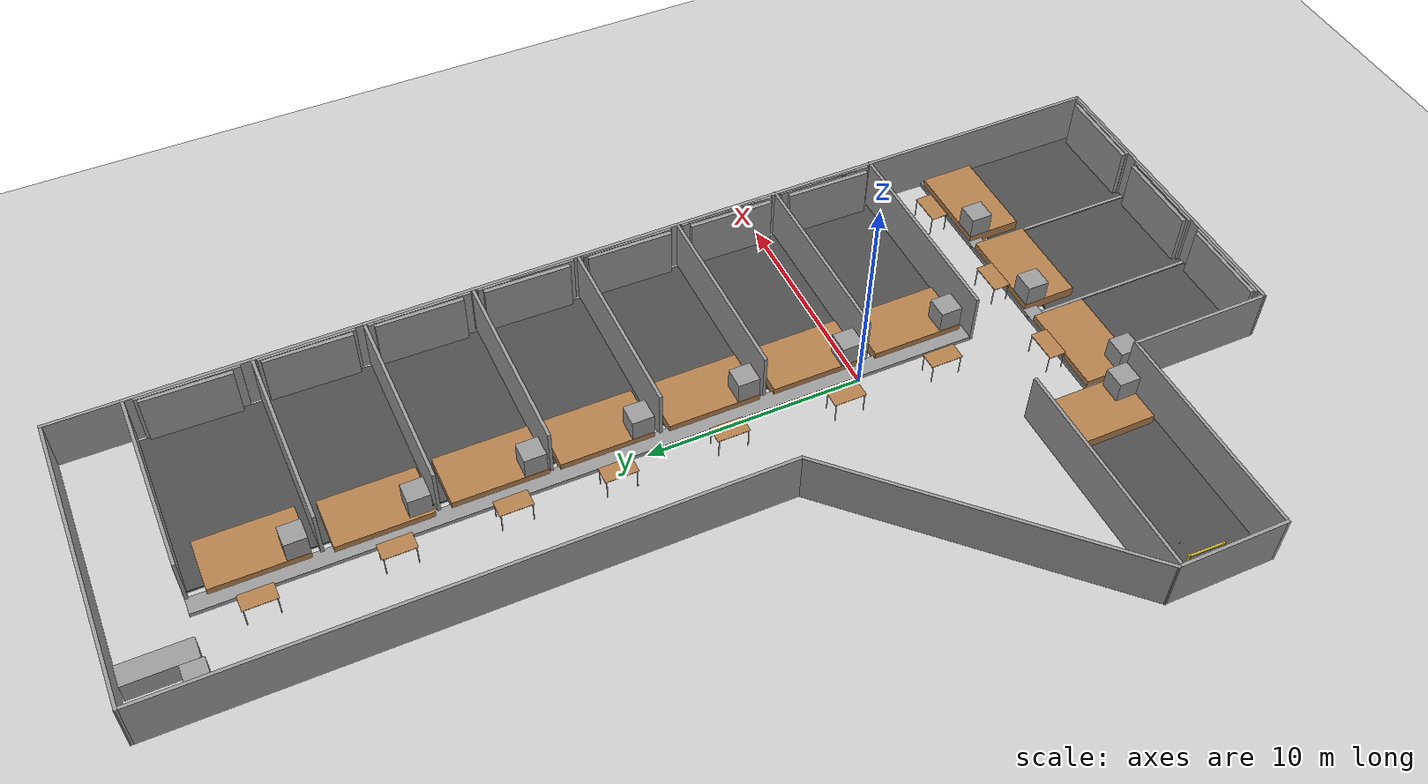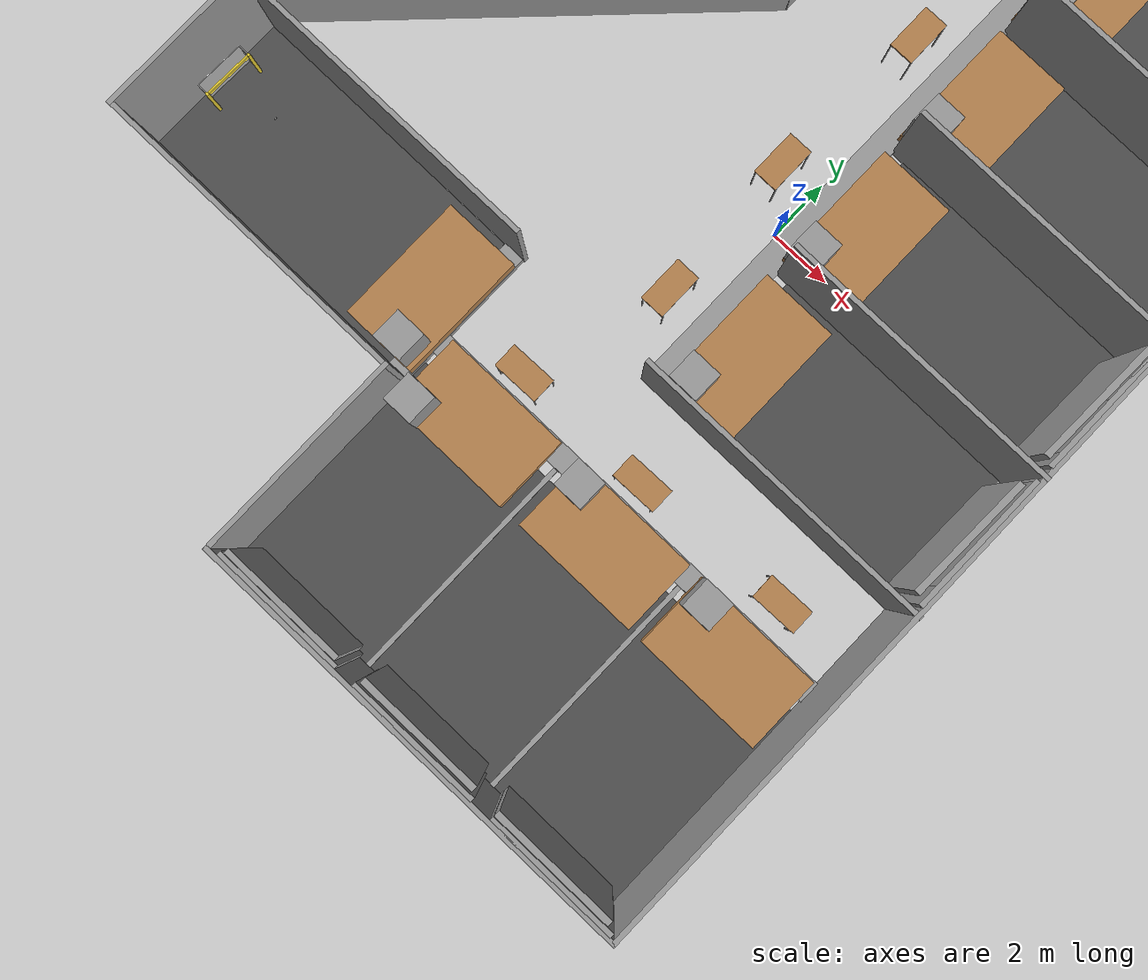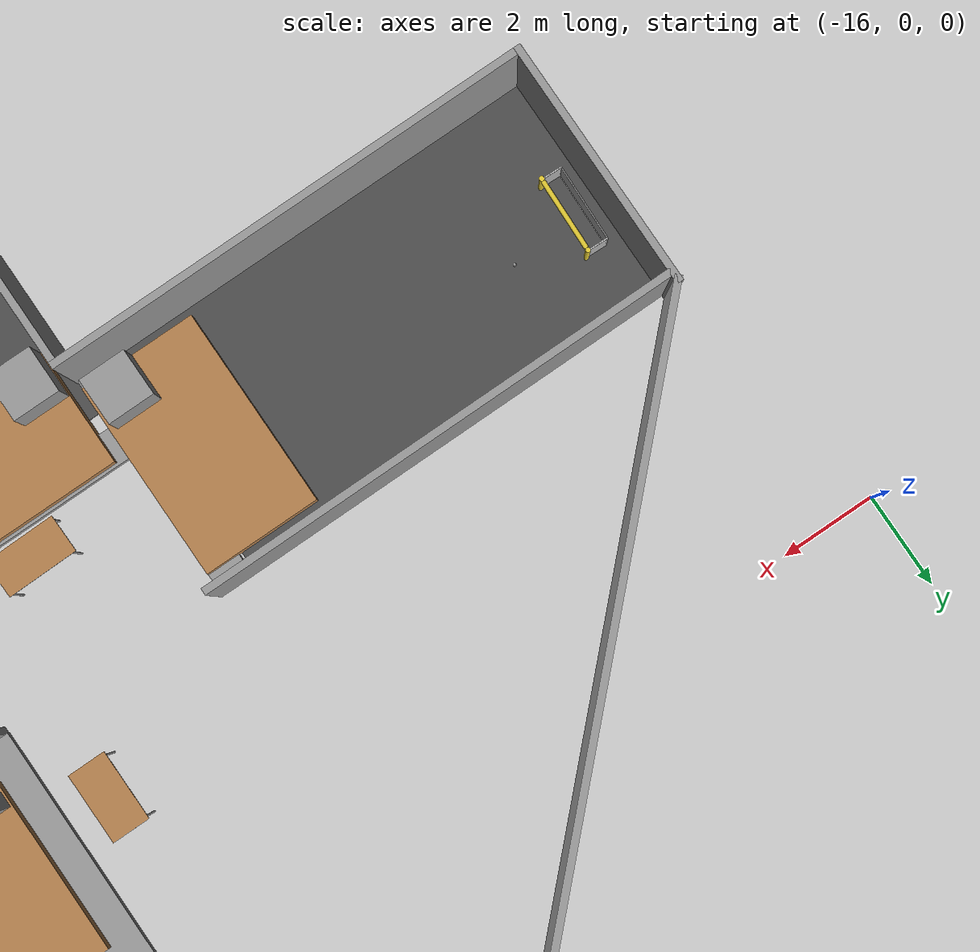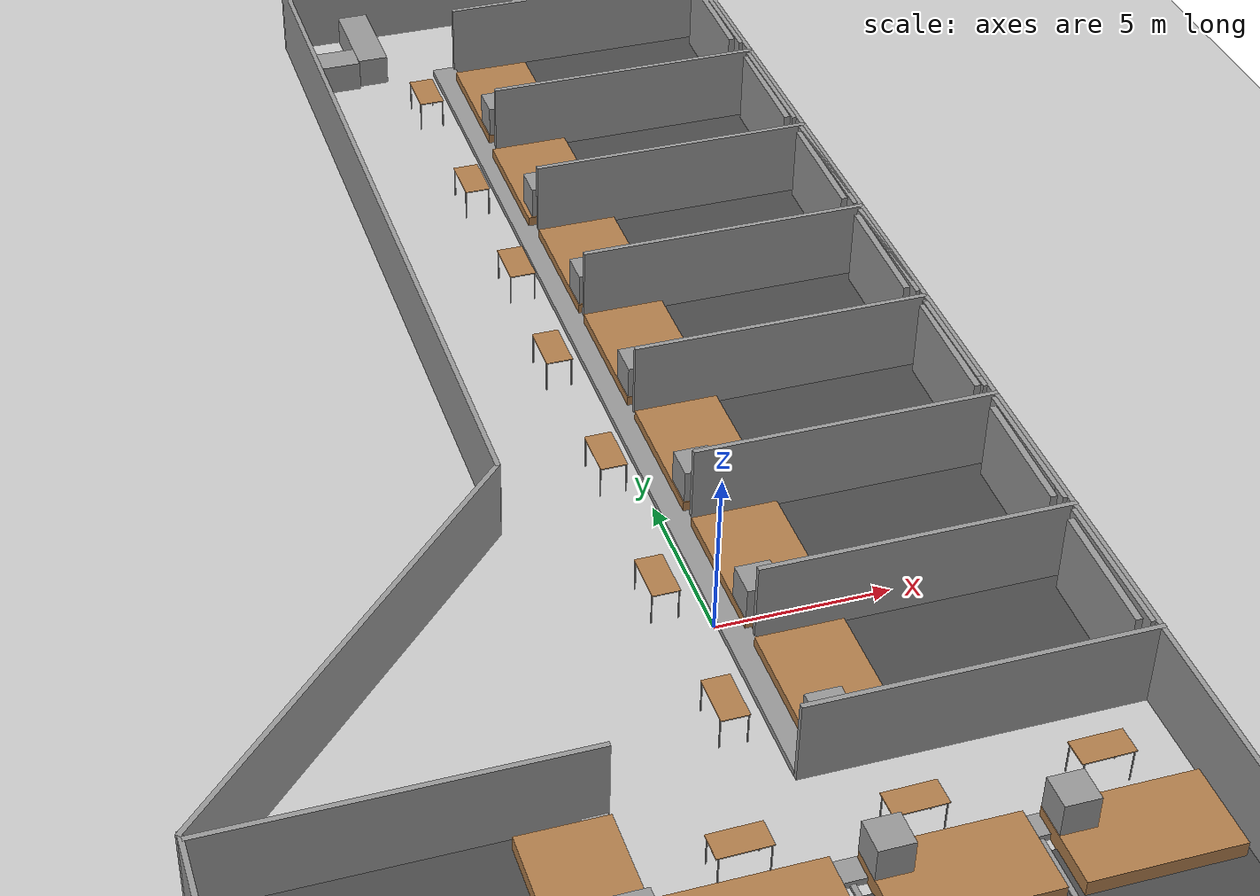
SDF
<sdf version="1.6">
 <world name="default">
  <light name="sun" type="directional">
   <pose>0 0 10 0 -0 0</pose>
   <diffuse>0.8 0.8 0.8 1</diffuse>
   <specular>0.2 0.2 0.2 1</specular>
   <attenuation>
    <range>1000</range>
    <constant>0.9</constant>
    <linear>0.01</linear>
    <quadratic>0.001</quadratic>
   </attenuation>
   <direction>-0.5 0.1 -0.9</direction>
  </light>
  <gravity>0 0 -9.8</gravity>
  <magnetic_field>6e-06 2.3e-05 -4.2e-05</magnetic_field>
  <atmosphere type="adiabatic"/>
  <physics name="default_physics" default="0" type="ode">
   <max_step_size>0.001</max_step_size>
   <real_time_factor>1</real_time_factor>
   <real_time_update_rate>1000</real_time_update_rate>
  </physics>
  <scene><ambient>0.4 0.4 0.4 1</ambient><background>0.7 0.7 0.7 1</background><shadows>1</shadows></scene>
  <audio><device>default</device></audio>
  <spherical_coordinates>
   <surface_model>EARTH_WGS84</surface_model>
   <latitude_deg>0</latitude_deg>
   <longitude_deg>0</longitude_deg>
   <elevation>0</elevation>
   <heading_deg>0</heading_deg>
  </spherical_coordinates>
  <model name="test__">
   <pose>-2.61572 7.75657 0 0 -0 0</pose>
   <link name="Wall_1">
    <collision name="Wall_1_Collision">
     <geometry><box><size>15 0.15 2.5</size></box></geometry>
     <pose>0 0 1.25 0 -0 0</pose>
    </collision>
    <visual name="Wall_1_Visual">
     <pose>0 0 1.25 0 -0 0</pose>
     <geometry><box><size>15 0.15 2.5</size></box></geometry>
     <material>
      <script><uri>file://media/materials/scripts/gazebo.material</uri><name>Gazebo/Grey</name></script>
      <ambient>1 1 1 1</ambient>
     </material>
     <meta><layer>0</layer></meta>
    </visual>
    <pose>-7.10691 -7.85176 0 0 -0 -2.35619</pose>
   </link>
   <link name="Wall_11">
    <collision name="Wall_11_Collision">
     <geometry><box><size>14.3012 0.15 2.5</size></box></geometry>
     <pose>0 0 1.25 0 -0 0</pose>
    </collision>
    <visual name="Wall_11_Visual">
     <pose>0 0 1.25 0 -0 0</pose>
     <geometry><box><size>14.3012 0.15 2.5</size></box></geometry>
     <material>
      <script><uri>file://media/materials/scripts/gazebo.material</uri><name>Gazebo/Grey</name></script>
      <ambient>1 1 1 1</ambient>
     </material>
     <meta><layer>0</layer></meta>
    </visual>
    <pose>5.26724 24.8122 0 0 -0 3.13958</pose>
   </link>
   <link name="Wall_12">
    <collision name="Wall_12_Collision">
     <geometry><box><size>27.5 0.15 2.5</size></box></geometry>
     <pose>0 0 1.25 0 -0 0</pose>
    </collision>
    <visual name="Wall_12_Visual">
     <pose>0 0 1.25 0 -0 0</pose>
     <geometry><box><size>27.5 0.15 2.5</size></box></geometry>
     <material>
      <script><uri>file://media/materials/scripts/gazebo.material</uri><name>Gazebo/Grey</name></script>
      <ambient>1 1 1 1</ambient>
     </material>
     <meta><layer>0</layer></meta>
    </visual>
    <pose>-1.80834 11.1571 0 0 -0 -1.5708</pose>
   </link>
   <link name="Wall_21">
    <collision name="Wall_21_Collision">
     <geometry><box><size>10.2504 0.15 2.5</size></box></geometry>
     <pose>0 0 1.25 0 -0 0</pose>
    </collision>
    <visual name="Wall_21_Visual">
     <pose>0 0 1.25 0 -0 0</pose>
     <geometry><box><size>10.2504 0.15 2.5</size></box></geometry>
     <material>
      <script><uri>file://media/materials/scripts/gazebo.material</uri><name>Gazebo/Grey</name></script>
      <ambient>1 1 1 1</ambient>
     </material>
     <meta><layer>0</layer></meta>
    </visual>
    <pose>-7.21776 -13.2674 0 0 -0 -3.14011</pose>
   </link>
   <link name="Wall_25">
    <collision name="Wall_25_Collision">
     <geometry><box><size>8.5 0.15 0.1</size></box></geometry>
     <pose>0 0 0.05 0 -0 0</pose>
    </collision>
    <visual name="Wall_25_Visual">
     <pose>0 0 0.05 0 -0 0</pose>
     <geometry><box><size>8.5 0.15 0.1</size></box></geometry>
     <material>
      <script><uri>file://media/materials/scripts/gazebo.material</uri><name>Gazebo/Grey</name></script>
      <ambient>1 1 1 1</ambient>
     </material>
     <meta><layer>0</layer></meta>
    </visual>
    <pose>2.73219 -20.5989 0 0 -0 -1.5708</pose>
   </link>
   <link name="Wall_27">
    <collision name="Wall_27_Collision">
     <geometry><box><size>8.5 0.15 0.1</size></box></geometry>
     <pose>0 0 0.05 0 -0 0</pose>
    </collision>
    <visual name="Wall_27_Visual">
     <pose>0 0 0.05 0 -0 0</pose>
     <geometry><box><size>8.5 0.15 0.1</size></box></geometry>
     <material>
      <script><uri>file://media/materials/scripts/gazebo.material</uri><name>Gazebo/Grey</name></script>
      <ambient>1 1 1 1</ambient>
     </material>
     <meta><layer>0</layer></meta>
    </visual>
    <pose>7.59109 -20.6044 0 0 -0 -1.5708</pose>
   </link>
   <link name="Wall_29">
    <collision name="Wall_29_Collision">
     <geometry><box><size>9.75 0.15 2.5</size></box></geometry>
     <pose>0 0 1.25 0 -0 0</pose>
    </collision>
    <visual name="Wall_29_Visual">
     <pose>0 0 1.25 0 -0 0</pose>
     <geometry><box><size>9.75 0.15 2.5</size></box></geometry>
     <material>
      <script><uri>file://media/materials/scripts/gazebo.material</uri><name>Gazebo/Grey</name></script>
      <ambient>1 1 1 1</ambient>
     </material>
     <meta><layer>0</layer></meta>
    </visual>
    <pose>7.56587 -13.406 0 0 -0 3.14159</pose>
   </link>
   <link name="Wall_3">
    <collision name="Wall_3_Collision">
     <geometry><box><size>5.25 0.15 2.5</size></box></geometry>
     <pose>0 0 1.25 0 -0 0</pose>
    </collision>
    <visual name="Wall_3_Visual">
     <pose>0 0 1.25 0 -0 0</pose>
     <geometry><box><size>5.25 0.15 2.5</size></box></geometry>
     <material>
      <script><uri>file://media/materials/scripts/gazebo.material</uri><name>Gazebo/Grey</name></script>
      <ambient>1 1 1 1</ambient>
     </material>
     <meta><layer>0</layer></meta>
    </visual>
    <pose>-12.3572 -15.652 0 0 -0 -1.5708</pose>
   </link>
   <link name="Wall_31">
    <collision name="Wall_31_Collision">
     <geometry><box><size>34.9 0.8 0.2</size></box></geometry>
     <pose>0 0 0.1 0 -0 0</pose>
    </collision>
    <visual name="Wall_31_Visual">
     <pose>0 0 0.1 0 -0 0</pose>
     <geometry><box><size>34.9 0.8 0.2</size></box></geometry>
     <material>
      <script><uri>file://media/materials/scripts/gazebo.material</uri><name>Gazebo/Grey</name></script>
      <ambient>1 1 1 1</ambient>
     </material>
     <meta><layer>0</layer></meta>
    </visual>
    <pose>3.07724 4.10911 0 0 -0 1.5708</pose>
   </link>
   <link name="Wall_33">
    <collision name="Wall_33_Collision">
     <geometry><box><size>9 0.15 2.5</size></box></geometry>
     <pose>0 0 1.25 0 -0 0</pose>
    </collision>
    <visual name="Wall_33_Visual">
     <pose>0 0 1.25 0 -0 0</pose>
     <geometry><box><size>9 0.15 2.5</size></box></geometry>
     <material>
      <script><uri>file://media/materials/scripts/gazebo.material</uri><name>Gazebo/Grey</name></script>
      <ambient>1 1 1 1</ambient>
     </material>
     <meta><layer>0</layer></meta>
    </visual>
    <pose>7.93132 -8.48567 0 0 -0 0</pose>
   </link>
   <link name="Wall_35">
    <collision name="Wall_35_Collision">
     <geometry><box><size>9 0.15 2.5</size></box></geometry>
     <pose>0 0 1.25 0 -0 0</pose>
    </collision>
    <visual name="Wall_35_Visual">
     <pose>0 0 1.25 0 -0 0</pose>
     <geometry><box><size>9 0.15 2.5</size></box></geometry>
     <material>
      <script><uri>file://media/materials/scripts/gazebo.material</uri><name>Gazebo/Grey</name></script>
      <ambient>1 1 1 1</ambient>
     </material>
     <meta><layer>0</layer></meta>
    </visual>
    <pose>7.91645 -3.54945 0 0 -0 0</pose>
   </link>
   <link name="Wall_37">
    <collision name="Wall_37_Collision">
     <geometry><box><size>9 0.15 2.5</size></box></geometry>
     <pose>0 0 1.25 0 -0 0</pose>
    </collision>
    <visual name="Wall_37_Visual">
     <pose>0 0 1.25 0 -0 0</pose>
     <geometry><box><size>9 0.15 2.5</size></box></geometry>
     <material>
      <script><uri>file://media/materials/scripts/gazebo.material</uri><name>Gazebo/Grey</name></script>
      <ambient>1 1 1 1</ambient>
     </material>
     <meta><layer>0</layer></meta>
    </visual>
    <pose>7.85698 1.29757 0 0 -0 0</pose>
   </link>
   <link name="Wall_39">
    <collision name="Wall_39_Collision">
     <geometry><box><size>9 0.15 2.5</size></box></geometry>
     <pose>0 0 1.25 0 -0 0</pose>
    </collision>
    <visual name="Wall_39_Visual">
     <pose>0 0 1.25 0 -0 0</pose>
     <geometry><box><size>9 0.15 2.5</size></box></geometry>
     <material>
      <script><uri>file://media/materials/scripts/gazebo.material</uri><name>Gazebo/Grey</name></script>
      <ambient>1 1 1 1</ambient>
     </material>
     <meta><layer>0</layer></meta>
    </visual>
    <pose>7.88083 6.21966 0 0 -0 0</pose>
   </link>
   <link name="Wall_4">
    <collision name="Wall_4_Collision">
     <geometry><box><size>10.3399 0.15 2.5</size></box></geometry>
     <pose>0 0 1.25 0 -0 0</pose>
    </collision>
    <visual name="Wall_4_Visual">
     <pose>0 0 1.25 0 -0 0</pose>
     <geometry><box><size>10.3399 0.15 2.5</size></box></geometry>
     <material>
      <script><uri>file://media/materials/scripts/gazebo.material</uri><name>Gazebo/Grey</name></script>
      <ambient>1 1 1 1</ambient>
     </material>
     <meta><layer>0</layer></meta>
    </visual>
    <pose>-7.26247 -18.202 0 0 -0 1.4e-05</pose>
   </link>
   <link name="Wall_41">
    <collision name="Wall_41_Collision">
     <geometry><box><size>9 0.15 2.5</size></box></geometry>
     <pose>0 0 1.25 0 -0 0</pose>
    </collision>
    <visual name="Wall_41_Visual">
     <pose>0 0 1.25 0 -0 0</pose>
     <geometry><box><size>9 0.15 2.5</size></box></geometry>
     <material>
      <script><uri>file://media/materials/scripts/gazebo.material</uri><name>Gazebo/Grey</name></script>
      <ambient>1 1 1 1</ambient>
     </material>
     <meta><layer>0</layer></meta>
    </visual>
    <pose>7.88083 11.1256 0 0 -0 0</pose>
   </link>
   <link name="Wall_43">
    <collision name="Wall_43_Collision">
     <geometry><box><size>9 0.15 2.5</size></box></geometry>
     <pose>0 0 1.25 0 -0 0</pose>
    </collision>
    <visual name="Wall_43_Visual">
     <pose>0 0 1.25 0 -0 0</pose>
     <geometry><box><size>9 0.15 2.5</size></box></geometry>
     <material>
      <script><uri>file://media/materials/scripts/gazebo.material</uri><name>Gazebo/Grey</name></script>
      <ambient>1 1 1 1</ambient>
     </material>
     <meta><layer>0</layer></meta>
    </visual>
    <pose>7.88083 16.0119 0 0 -0 0</pose>
   </link>
   <link name="Wall_45">
    <collision name="Wall_45_Collision">
     <geometry><box><size>9 0.15 2.5</size></box></geometry>
     <pose>0 0 1.25 0 -0 0</pose>
    </collision>
    <visual name="Wall_45_Visual">
     <pose>0 0 1.25 0 -0 0</pose>
     <geometry><box><size>9 0.15 2.5</size></box></geometry>
     <material>
      <script><uri>file://media/materials/scripts/gazebo.material</uri><name>Gazebo/Grey</name></script>
      <ambient>1 1 1 1</ambient>
     </material>
     <meta><layer>0</layer></meta>
    </visual>
    <pose>7.91033 21.4782 0 0 -0 0</pose>
   </link>
   <link name="Wall_49">
    <collision name="Wall_49_Collision">
     <geometry><box><size>5 0.7 0.2</size></box></geometry>
     <pose>0 0 0.1 0 -0 0</pose>
    </collision>
    <visual name="Wall_49_Visual">
     <pose>0 0 0.1 0 -0 0</pose>
     <geometry><box><size>5 0.7 0.2</size></box></geometry>
     <material>
      <script><uri>file://media/materials/scripts/gazebo.material</uri><name>Gazebo/Grey</name></script>
      <ambient>1 1 1 1</ambient>
     </material>
     <meta><layer>0</layer></meta>
    </visual>
    <pose>-2.47472 -15.7158 0 0 -0 1.5708</pose>
   </link>
   <link name="Wall_51">
    <collision name="Wall_51_Collision">
     <geometry><box><size>14.75 0.7 0.2</size></box></geometry>
     <pose>0 0 0.1 0 -0 0</pose>
    </collision>
    <visual name="Wall_51_Visual">
     <pose>0 0 0.1 0 -0 0</pose>
     <geometry><box><size>14.75 0.7 0.2</size></box></geometry>
     <material>
      <script><uri>file://media/materials/scripts/gazebo.material</uri><name>Gazebo/Grey</name></script>
      <ambient>1 1 1 1</ambient>
     </material>
     <meta><layer>0</layer></meta>
    </visual>
    <pose>5.08824 -16.7089 0 0 -0 0</pose>
   </link>
   <link name="Wall_7">
    <collision name="Wall_7_Collision">
     <geometry><box><size>6.75 0.15 2.5</size></box></geometry>
     <pose>0 0 1.25 0 -0 0</pose>
    </collision>
    <visual name="Wall_7_Visual">
     <pose>0 0 1.25 0 -0 0</pose>
     <geometry><box><size>6.75 0.15 2.5</size></box></geometry>
     <material>
      <script><uri>file://media/materials/scripts/gazebo.material</uri><name>Gazebo/Grey</name></script>
      <ambient>1 1 1 1</ambient>
     </material>
     <meta><layer>0</layer></meta>
    </visual>
    <pose>-2.16761 -21.502 0 0 -0 -1.57075</pose>
   </link>
   <link name="Wall_8">
    <collision name="Wall_8_Collision">
     <geometry><box><size>14.6604 0.15 2.5</size></box></geometry>
     <pose>0 0 1.25 0 -0 0</pose>
    </collision>
    <visual name="Wall_8_Visual">
     <pose>0 0 1.25 0 -0 0</pose>
     <geometry><box><size>14.6604 0.15 2.5</size></box></geometry>
     <material>
      <script><uri>file://media/materials/scripts/gazebo.material</uri><name>Gazebo/Grey</name></script>
      <ambient>1 1 1 1</ambient>
     </material>
     <meta><layer>0</layer></meta>
    </visual>
    <pose>5.08768 -24.817 0 0 -0 0.002061</pose>
   </link>
   <link name="Wall_9">
    <collision name="Wall_9_Collision">
     <geometry><box><size>49.75 0.15 2.5</size></box></geometry>
     <pose>0 0 1.25 0 -0 0</pose>
    </collision>
    <visual name="Wall_9_Visual">
     <pose>0 0 1.25 0 -0 0</pose>
     <geometry><box><size>49.75 0.15 2.5</size></box></geometry>
     <material>
      <script><uri>file://media/materials/scripts/gazebo.material</uri><name>Gazebo/Grey</name></script>
      <ambient>1 1 1 1</ambient>
     </material>
     <meta><layer>0</layer></meta>
    </visual>
    <pose>12.3428 -0.002026 0 0 -0 1.5708</pose>
   </link>
   <static>1</static>
  </model>
  <model name="ground_plane">
   <static>1</static>
   <link name="link">
    <collision name="collision">
     <geometry><plane><normal>0 0 1</normal><size>100 100</size></plane></geometry>
     <surface>
      <contact><collide_bitmask>65535</collide_bitmask></contact>
      <friction><ode><mu>100</mu><mu2>50</mu2></ode></friction>
     </surface>
    </collision>
    <visual name="visual">
     <cast_shadows>0</cast_shadows>
     <geometry><plane><normal>0 0 1</normal><size>100 100</size></plane></geometry>
     <material>
      <script><uri>file://media/materials/scripts/gazebo.material</uri><name>Gazebo/Grey</name></script>
     </material>
    </visual>
   </link>
   <pose>-3.51447 11.9136 0 0 -0 0</pose>
  </model>
  <model name="table_clone">
   <static>1</static>
   <link name="link">
    <collision name="surface">
     <pose>0 0 1 0 -0 0</pose>
     <geometry><box><size>1.5 0.8 0.03</size></box></geometry>
     <surface><friction><ode><mu>0.6</mu><mu2>0.6</mu2></ode></friction></surface>
    </collision>
    <visual name="visual1">
     <pose>0 0 1 0 -0 0</pose>
     <geometry><box><size>1.5 0.8 0.03</size></box></geometry>
     <material>
      <script><uri>file://media/materials/scripts/gazebo.material</uri><name>Gazebo/Wood</name></script>
     </material>
    </visual>
    <collision name="front_left_leg">
     <pose>0.68 0.38 0.5 0 -0 0</pose>
     <geometry><cylinder><radius>0.02</radius><length>1</length></cylinder></geometry>
    </collision>
    <visual name="front_left_leg">
     <pose>0.68 0.38 0.5 0 -0 0</pose>
     <geometry><cylinder><radius>0.02</radius><length>1</length></cylinder></geometry>
     <material>
      <script><uri>file://media/materials/scripts/gazebo.material</uri><name>Gazebo/Grey</name></script>
     </material>
    </visual>
    <collision name="front_right_leg">
     <pose>0.68 -0.38 0.5 0 -0 0</pose>
     <geometry><cylinder><radius>0.02</radius><length>1</length></cylinder></geometry>
    </collision>
    <visual name="front_right_leg">
     <pose>0.68 -0.38 0.5 0 -0 0</pose>
     <geometry><cylinder><radius>0.02</radius><length>1</length></cylinder></geometry>
     <material>
      <script><uri>file://media/materials/scripts/gazebo.material</uri><name>Gazebo/Grey</name></script>
     </material>
    </visual>
    <collision name="back_right_leg">
     <pose>-0.68 -0.38 0.5 0 -0 0</pose>
     <geometry><cylinder><radius>0.02</radius><length>1</length></cylinder></geometry>
    </collision>
    <visual name="back_right_leg">
     <pose>-0.68 -0.38 0.5 0 -0 0</pose>
     <geometry><cylinder><radius>0.02</radius><length>1</length></cylinder></geometry>
     <material>
      <script><uri>file://media/materials/scripts/gazebo.material</uri><name>Gazebo/Grey</name></script>
     </material>
    </visual>
    <collision name="back_left_leg">
     <pose>-0.68 0.38 0.5 0 -0 0</pose>
     <geometry><cylinder><radius>0.02</radius><length>1</length></cylinder></geometry>
    </collision>
    <visual name="back_left_leg">
     <pose>-0.68 0.38 0.5 0 -0 0</pose>
     <geometry><cylinder><radius>0.02</radius><length>1</length></cylinder></geometry>
     <material>
      <script><uri>file://media/materials/scripts/gazebo.material</uri><name>Gazebo/Grey</name></script>
     </material>
    </visual>
   </link>
   <pose>-1.16496 1.3236 0 0 0 -1.56764</pose>
  </model>
  <model name="table_clone_clone">
   <static>1</static>
   <link name="link">
    <collision name="surface">
     <pose>0 0 1 0 -0 0</pose>
     <geometry><box><size>1.5 0.8 0.03</size></box></geometry>
     <surface><friction><ode><mu>0.6</mu><mu2>0.6</mu2></ode></friction></surface>
    </collision>
    <visual name="visual1">
     <pose>0 0 1 0 -0 0</pose>
     <geometry><box><size>1.5 0.8 0.03</size></box></geometry>
     <material>
      <script><uri>file://media/materials/scripts/gazebo.material</uri><name>Gazebo/Wood</name></script>
     </material>
    </visual>
    <collision name="front_left_leg">
     <pose>0.68 0.38 0.5 0 -0 0</pose>
     <geometry><cylinder><radius>0.02</radius><length>1</length></cylinder></geometry>
    </collision>
    <visual name="front_left_leg">
     <pose>0.68 0.38 0.5 0 -0 0</pose>
     <geometry><cylinder><radius>0.02</radius><length>1</length></cylinder></geometry>
     <material>
      <script><uri>file://media/materials/scripts/gazebo.material</uri><name>Gazebo/Grey</name></script>
     </material>
    </visual>
    <collision name="front_right_leg">
     <pose>0.68 -0.38 0.5 0 -0 0</pose>
     <geometry><cylinder><radius>0.02</radius><length>1</length></cylinder></geometry>
    </collision>
    <visual name="front_right_leg">
     <pose>0.68 -0.38 0.5 0 -0 0</pose>
     <geometry><cylinder><radius>0.02</radius><length>1</length></cylinder></geometry>
     <material>
      <script><uri>file://media/materials/scripts/gazebo.material</uri><name>Gazebo/Grey</name></script>
     </material>
    </visual>
    <collision name="back_right_leg">
     <pose>-0.68 -0.38 0.5 0 -0 0</pose>
     <geometry><cylinder><radius>0.02</radius><length>1</length></cylinder></geometry>
    </collision>
    <visual name="back_right_leg">
     <pose>-0.68 -0.38 0.5 0 -0 0</pose>
     <geometry><cylinder><radius>0.02</radius><length>1</length></cylinder></geometry>
     <material>
      <script><uri>file://media/materials/scripts/gazebo.material</uri><name>Gazebo/Grey</name></script>
     </material>
    </visual>
    <collision name="back_left_leg">
     <pose>-0.68 0.38 0.5 0 -0 0</pose>
     <geometry><cylinder><radius>0.02</radius><length>1</length></cylinder></geometry>
    </collision>
    <visual name="back_left_leg">
     <pose>-0.68 0.38 0.5 0 -0 0</pose>
     <geometry><cylinder><radius>0.02</radius><length>1</length></cylinder></geometry>
     <material>
      <script><uri>file://media/materials/scripts/gazebo.material</uri><name>Gazebo/Grey</name></script>
     </material>
    </visual>
   </link>
   <pose>-0.995575 -3.46829 0 0 0 -1.56764</pose>
  </model>
  <model name="table_clone_clone_0">
   <static>1</static>
   <link name="link">
    <collision name="surface">
     <pose>0 0 1 0 -0 0</pose>
     <geometry><box><size>1.5 0.8 0.03</size></box></geometry>
     <surface><friction><ode><mu>0.6</mu><mu2>0.6</mu2></ode></friction></surface>
    </collision>
    <visual name="visual1">
     <pose>0 0 1 0 -0 0</pose>
     <geometry><box><size>1.5 0.8 0.03</size></box></geometry>
     <material>
      <script><uri>file://media/materials/scripts/gazebo.material</uri><name>Gazebo/Wood</name></script>
     </material>
    </visual>
    <collision name="front_left_leg">
     <pose>0.68 0.38 0.5 0 -0 0</pose>
     <geometry><cylinder><radius>0.02</radius><length>1</length></cylinder></geometry>
    </collision>
    <visual name="front_left_leg">
     <pose>0.68 0.38 0.5 0 -0 0</pose>
     <geometry><cylinder><radius>0.02</radius><length>1</length></cylinder></geometry>
     <material>
      <script><uri>file://media/materials/scripts/gazebo.material</uri><name>Gazebo/Grey</name></script>
     </material>
    </visual>
    <collision name="front_right_leg">
     <pose>0.68 -0.38 0.5 0 -0 0</pose>
     <geometry><cylinder><radius>0.02</radius><length>1</length></cylinder></geometry>
    </collision>
    <visual name="front_right_leg">
     <pose>0.68 -0.38 0.5 0 -0 0</pose>
     <geometry><cylinder><radius>0.02</radius><length>1</length></cylinder></geometry>
     <material>
      <script><uri>file://media/materials/scripts/gazebo.material</uri><name>Gazebo/Grey</name></script>
     </material>
    </visual>
    <collision name="back_right_leg">
     <pose>-0.68 -0.38 0.5 0 -0 0</pose>
     <geometry><cylinder><radius>0.02</radius><length>1</length></cylinder></geometry>
    </collision>
    <visual name="back_right_leg">
     <pose>-0.68 -0.38 0.5 0 -0 0</pose>
     <geometry><cylinder><radius>0.02</radius><length>1</length></cylinder></geometry>
     <material>
      <script><uri>file://media/materials/scripts/gazebo.material</uri><name>Gazebo/Grey</name></script>
     </material>
    </visual>
    <collision name="back_left_leg">
     <pose>-0.68 0.38 0.5 0 -0 0</pose>
     <geometry><cylinder><radius>0.02</radius><length>1</length></cylinder></geometry>
    </collision>
    <visual name="back_left_leg">
     <pose>-0.68 0.38 0.5 0 -0 0</pose>
     <geometry><cylinder><radius>0.02</radius><length>1</length></cylinder></geometry>
     <material>
      <script><uri>file://media/materials/scripts/gazebo.material</uri><name>Gazebo/Grey</name></script>
     </material>
    </visual>
   </link>
   <pose>-0.876309 6.63945 0 0 0 -1.56764</pose>
  </model>
  <model name="table_clone_clone_1">
   <static>1</static>
   <link name="link">
    <collision name="surface">
     <pose>0 0 1 0 -0 0</pose>
     <geometry><box><size>1.5 0.8 0.03</size></box></geometry>
     <surface><friction><ode><mu>0.6</mu><mu2>0.6</mu2></ode></friction></surface>
    </collision>
    <visual name="visual1">
     <pose>0 0 1 0 -0 0</pose>
     <geometry><box><size>1.5 0.8 0.03</size></box></geometry>
     <material>
      <script><uri>file://media/materials/scripts/gazebo.material</uri><name>Gazebo/Wood</name></script>
     </material>
    </visual>
    <collision name="front_left_leg">
     <pose>0.68 0.38 0.5 0 -0 0</pose>
     <geometry><cylinder><radius>0.02</radius><length>1</length></cylinder></geometry>
    </collision>
    <visual name="front_left_leg">
     <pose>0.68 0.38 0.5 0 -0 0</pose>
     <geometry><cylinder><radius>0.02</radius><length>1</length></cylinder></geometry>
     <material>
      <script><uri>file://media/materials/scripts/gazebo.material</uri><name>Gazebo/Grey</name></script>
     </material>
    </visual>
    <collision name="front_right_leg">
     <pose>0.68 -0.38 0.5 0 -0 0</pose>
     <geometry><cylinder><radius>0.02</radius><length>1</length></cylinder></geometry>
    </collision>
    <visual name="front_right_leg">
     <pose>0.68 -0.38 0.5 0 -0 0</pose>
     <geometry><cylinder><radius>0.02</radius><length>1</length></cylinder></geometry>
     <material>
      <script><uri>file://media/materials/scripts/gazebo.material</uri><name>Gazebo/Grey</name></script>
     </material>
    </visual>
    <collision name="back_right_leg">
     <pose>-0.68 -0.38 0.5 0 -0 0</pose>
     <geometry><cylinder><radius>0.02</radius><length>1</length></cylinder></geometry>
    </collision>
    <visual name="back_right_leg">
     <pose>-0.68 -0.38 0.5 0 -0 0</pose>
     <geometry><cylinder><radius>0.02</radius><length>1</length></cylinder></geometry>
     <material>
      <script><uri>file://media/materials/scripts/gazebo.material</uri><name>Gazebo/Grey</name></script>
     </material>
    </visual>
    <collision name="back_left_leg">
     <pose>-0.68 0.38 0.5 0 -0 0</pose>
     <geometry><cylinder><radius>0.02</radius><length>1</length></cylinder></geometry>
    </collision>
    <visual name="back_left_leg">
     <pose>-0.68 0.38 0.5 0 -0 0</pose>
     <geometry><cylinder><radius>0.02</radius><length>1</length></cylinder></geometry>
     <material>
      <script><uri>file://media/materials/scripts/gazebo.material</uri><name>Gazebo/Grey</name></script>
     </material>
    </visual>
   </link>
   <pose>-0.911845 11.6947 0 0 0 -1.56764</pose>
  </model>
  <model name="table_clone_clone_2">
   <static>1</static>
   <link name="link">
    <collision name="surface">
     <pose>0 0 1 0 -0 0</pose>
     <geometry><box><size>1.5 0.8 0.03</size></box></geometry>
     <surface><friction><ode><mu>0.6</mu><mu2>0.6</mu2></ode></friction></surface>
    </collision>
    <visual name="visual1">
     <pose>0 0 1 0 -0 0</pose>
     <geometry><box><size>1.5 0.8 0.03</size></box></geometry>
     <material>
      <script><uri>file://media/materials/scripts/gazebo.material</uri><name>Gazebo/Wood</name></script>
     </material>
    </visual>
    <collision name="front_left_leg">
     <pose>0.68 0.38 0.5 0 -0 0</pose>
     <geometry><cylinder><radius>0.02</radius><length>1</length></cylinder></geometry>
    </collision>
    <visual name="front_left_leg">
     <pose>0.68 0.38 0.5 0 -0 0</pose>
     <geometry><cylinder><radius>0.02</radius><length>1</length></cylinder></geometry>
     <material>
      <script><uri>file://media/materials/scripts/gazebo.material</uri><name>Gazebo/Grey</name></script>
     </material>
    </visual>
    <collision name="front_right_leg">
     <pose>0.68 -0.38 0.5 0 -0 0</pose>
     <geometry><cylinder><radius>0.02</radius><length>1</length></cylinder></geometry>
    </collision>
    <visual name="front_right_leg">
     <pose>0.68 -0.38 0.5 0 -0 0</pose>
     <geometry><cylinder><radius>0.02</radius><length>1</length></cylinder></geometry>
     <material>
      <script><uri>file://media/materials/scripts/gazebo.material</uri><name>Gazebo/Grey</name></script>
     </material>
    </visual>
    <collision name="back_right_leg">
     <pose>-0.68 -0.38 0.5 0 -0 0</pose>
     <geometry><cylinder><radius>0.02</radius><length>1</length></cylinder></geometry>
    </collision>
    <visual name="back_right_leg">
     <pose>-0.68 -0.38 0.5 0 -0 0</pose>
     <geometry><cylinder><radius>0.02</radius><length>1</length></cylinder></geometry>
     <material>
      <script><uri>file://media/materials/scripts/gazebo.material</uri><name>Gazebo/Grey</name></script>
     </material>
    </visual>
    <collision name="back_left_leg">
     <pose>-0.68 0.38 0.5 0 -0 0</pose>
     <geometry><cylinder><radius>0.02</radius><length>1</length></cylinder></geometry>
    </collision>
    <visual name="back_left_leg">
     <pose>-0.68 0.38 0.5 0 -0 0</pose>
     <geometry><cylinder><radius>0.02</radius><length>1</length></cylinder></geometry>
     <material>
      <script><uri>file://media/materials/scripts/gazebo.material</uri><name>Gazebo/Grey</name></script>
     </material>
    </visual>
   </link>
   <pose>-0.712305 16.1839 0 0 0 -1.56764</pose>
  </model>
  <model name="table_clone_clone_3">
   <static>1</static>
   <link name="link">
    <collision name="surface">
     <pose>0 0 1 0 -0 0</pose>
     <geometry><box><size>1.5 0.8 0.03</size></box></geometry>
     <surface><friction><ode><mu>0.6</mu><mu2>0.6</mu2></ode></friction></surface>
    </collision>
    <visual name="visual1">
     <pose>0 0 1 0 -0 0</pose>
     <geometry><box><size>1.5 0.8 0.03</size></box></geometry>
     <material>
      <script><uri>file://media/materials/scripts/gazebo.material</uri><name>Gazebo/Wood</name></script>
     </material>
    </visual>
    <collision name="front_left_leg">
     <pose>0.68 0.38 0.5 0 -0 0</pose>
     <geometry><cylinder><radius>0.02</radius><length>1</length></cylinder></geometry>
    </collision>
    <visual name="front_left_leg">
     <pose>0.68 0.38 0.5 0 -0 0</pose>
     <geometry><cylinder><radius>0.02</radius><length>1</length></cylinder></geometry>
     <material>
      <script><uri>file://media/materials/scripts/gazebo.material</uri><name>Gazebo/Grey</name></script>
     </material>
    </visual>
    <collision name="front_right_leg">
     <pose>0.68 -0.38 0.5 0 -0 0</pose>
     <geometry><cylinder><radius>0.02</radius><length>1</length></cylinder></geometry>
    </collision>
    <visual name="front_right_leg">
     <pose>0.68 -0.38 0.5 0 -0 0</pose>
     <geometry><cylinder><radius>0.02</radius><length>1</length></cylinder></geometry>
     <material>
      <script><uri>file://media/materials/scripts/gazebo.material</uri><name>Gazebo/Grey</name></script>
     </material>
    </visual>
    <collision name="back_right_leg">
     <pose>-0.68 -0.38 0.5 0 -0 0</pose>
     <geometry><cylinder><radius>0.02</radius><length>1</length></cylinder></geometry>
    </collision>
    <visual name="back_right_leg">
     <pose>-0.68 -0.38 0.5 0 -0 0</pose>
     <geometry><cylinder><radius>0.02</radius><length>1</length></cylinder></geometry>
     <material>
      <script><uri>file://media/materials/scripts/gazebo.material</uri><name>Gazebo/Grey</name></script>
     </material>
    </visual>
    <collision name="back_left_leg">
     <pose>-0.68 0.38 0.5 0 -0 0</pose>
     <geometry><cylinder><radius>0.02</radius><length>1</length></cylinder></geometry>
    </collision>
    <visual name="back_left_leg">
     <pose>-0.68 0.38 0.5 0 -0 0</pose>
     <geometry><cylinder><radius>0.02</radius><length>1</length></cylinder></geometry>
     <material>
      <script><uri>file://media/materials/scripts/gazebo.material</uri><name>Gazebo/Grey</name></script>
     </material>
    </visual>
   </link>
   <pose>-0.788007 21.0863 0 0 0 -1.56764</pose>
  </model>
  <model name="table_clone_clone_4">
   <static>1</static>
   <link name="link">
    <collision name="surface">
     <pose>0 0 1 0 -0 0</pose>
     <geometry><box><size>1.5 0.8 0.03</size></box></geometry>
     <surface><friction><ode><mu>0.6</mu><mu2>0.6</mu2></ode></friction></surface>
    </collision>
    <visual name="visual1">
     <pose>0 0 1 0 -0 0</pose>
     <geometry><box><size>1.5 0.8 0.03</size></box></geometry>
     <material>
      <script><uri>file://media/materials/scripts/gazebo.material</uri><name>Gazebo/Wood</name></script>
     </material>
    </visual>
    <collision name="front_left_leg">
     <pose>0.68 0.38 0.5 0 -0 0</pose>
     <geometry><cylinder><radius>0.02</radius><length>1</length></cylinder></geometry>
    </collision>
    <visual name="front_left_leg">
     <pose>0.68 0.38 0.5 0 -0 0</pose>
     <geometry><cylinder><radius>0.02</radius><length>1</length></cylinder></geometry>
     <material>
      <script><uri>file://media/materials/scripts/gazebo.material</uri><name>Gazebo/Grey</name></script>
     </material>
    </visual>
    <collision name="front_right_leg">
     <pose>0.68 -0.38 0.5 0 -0 0</pose>
     <geometry><cylinder><radius>0.02</radius><length>1</length></cylinder></geometry>
    </collision>
    <visual name="front_right_leg">
     <pose>0.68 -0.38 0.5 0 -0 0</pose>
     <geometry><cylinder><radius>0.02</radius><length>1</length></cylinder></geometry>
     <material>
      <script><uri>file://media/materials/scripts/gazebo.material</uri><name>Gazebo/Grey</name></script>
     </material>
    </visual>
    <collision name="back_right_leg">
     <pose>-0.68 -0.38 0.5 0 -0 0</pose>
     <geometry><cylinder><radius>0.02</radius><length>1</length></cylinder></geometry>
    </collision>
    <visual name="back_right_leg">
     <pose>-0.68 -0.38 0.5 0 -0 0</pose>
     <geometry><cylinder><radius>0.02</radius><length>1</length></cylinder></geometry>
     <material>
      <script><uri>file://media/materials/scripts/gazebo.material</uri><name>Gazebo/Grey</name></script>
     </material>
    </visual>
    <collision name="back_left_leg">
     <pose>-0.68 0.38 0.5 0 -0 0</pose>
     <geometry><cylinder><radius>0.02</radius><length>1</length></cylinder></geometry>
    </collision>
    <visual name="back_left_leg">
     <pose>-0.68 0.38 0.5 0 -0 0</pose>
     <geometry><cylinder><radius>0.02</radius><length>1</length></cylinder></geometry>
     <material>
      <script><uri>file://media/materials/scripts/gazebo.material</uri><name>Gazebo/Grey</name></script>
     </material>
    </visual>
   </link>
   <pose>-0.831744 26.6989 0 0 0 -1.56764</pose>
  </model>
  <model name="table_clone_clone_5">
   <static>1</static>
   <link name="link">
    <collision name="surface">
     <pose>0 0 1 0 -0 0</pose>
     <geometry><box><size>1.5 0.8 0.03</size></box></geometry>
     <surface><friction><ode><mu>0.6</mu><mu2>0.6</mu2></ode></friction></surface>
    </collision>
    <visual name="visual1">
     <pose>0 0 1 0 -0 0</pose>
     <geometry><box><size>1.5 0.8 0.03</size></box></geometry>
     <material>
      <script><uri>file://media/materials/scripts/gazebo.material</uri><name>Gazebo/Wood</name></script>
     </material>
    </visual>
    <collision name="front_left_leg">
     <pose>0.68 0.38 0.5 0 -0 0</pose>
     <geometry><cylinder><radius>0.02</radius><length>1</length></cylinder></geometry>
    </collision>
    <visual name="front_left_leg">
     <pose>0.68 0.38 0.5 0 -0 0</pose>
     <geometry><cylinder><radius>0.02</radius><length>1</length></cylinder></geometry>
     <material>
      <script><uri>file://media/materials/scripts/gazebo.material</uri><name>Gazebo/Grey</name></script>
     </material>
    </visual>
    <collision name="front_right_leg">
     <pose>0.68 -0.38 0.5 0 -0 0</pose>
     <geometry><cylinder><radius>0.02</radius><length>1</length></cylinder></geometry>
    </collision>
    <visual name="front_right_leg">
     <pose>0.68 -0.38 0.5 0 -0 0</pose>
     <geometry><cylinder><radius>0.02</radius><length>1</length></cylinder></geometry>
     <material>
      <script><uri>file://media/materials/scripts/gazebo.material</uri><name>Gazebo/Grey</name></script>
     </material>
    </visual>
    <collision name="back_right_leg">
     <pose>-0.68 -0.38 0.5 0 -0 0</pose>
     <geometry><cylinder><radius>0.02</radius><length>1</length></cylinder></geometry>
    </collision>
    <visual name="back_right_leg">
     <pose>-0.68 -0.38 0.5 0 -0 0</pose>
     <geometry><cylinder><radius>0.02</radius><length>1</length></cylinder></geometry>
     <material>
      <script><uri>file://media/materials/scripts/gazebo.material</uri><name>Gazebo/Grey</name></script>
     </material>
    </visual>
    <collision name="back_left_leg">
     <pose>-0.68 0.38 0.5 0 -0 0</pose>
     <geometry><cylinder><radius>0.02</radius><length>1</length></cylinder></geometry>
    </collision>
    <visual name="back_left_leg">
     <pose>-0.68 0.38 0.5 0 -0 0</pose>
     <geometry><cylinder><radius>0.02</radius><length>1</length></cylinder></geometry>
     <material>
      <script><uri>file://media/materials/scripts/gazebo.material</uri><name>Gazebo/Grey</name></script>
     </material>
    </visual>
   </link>
   <pose>7.26268 -7.72077 0 0 -0 0.016845</pose>
  </model>
  <model name="table_clone_clone_5_clone">
   <static>1</static>
   <link name="link">
    <collision name="surface">
     <pose>0 0 1 0 -0 0</pose>
     <geometry><box><size>1.5 0.8 0.03</size></box></geometry>
     <surface><friction><ode><mu>0.6</mu><mu2>0.6</mu2></ode></friction></surface>
    </collision>
    <visual name="visual1">
     <pose>0 0 1 0 -0 0</pose>
     <geometry><box><size>1.5 0.8 0.03</size></box></geometry>
     <material>
      <script><uri>file://media/materials/scripts/gazebo.material</uri><name>Gazebo/Wood</name></script>
     </material>
    </visual>
    <collision name="front_left_leg">
     <pose>0.68 0.38 0.5 0 -0 0</pose>
     <geometry><cylinder><radius>0.02</radius><length>1</length></cylinder></geometry>
    </collision>
    <visual name="front_left_leg">
     <pose>0.68 0.38 0.5 0 -0 0</pose>
     <geometry><cylinder><radius>0.02</radius><length>1</length></cylinder></geometry>
     <material>
      <script><uri>file://media/materials/scripts/gazebo.material</uri><name>Gazebo/Grey</name></script>
     </material>
    </visual>
    <collision name="front_right_leg">
     <pose>0.68 -0.38 0.5 0 -0 0</pose>
     <geometry><cylinder><radius>0.02</radius><length>1</length></cylinder></geometry>
    </collision>
    <visual name="front_right_leg">
     <pose>0.68 -0.38 0.5 0 -0 0</pose>
     <geometry><cylinder><radius>0.02</radius><length>1</length></cylinder></geometry>
     <material>
      <script><uri>file://media/materials/scripts/gazebo.material</uri><name>Gazebo/Grey</name></script>
     </material>
    </visual>
    <collision name="back_right_leg">
     <pose>-0.68 -0.38 0.5 0 -0 0</pose>
     <geometry><cylinder><radius>0.02</radius><length>1</length></cylinder></geometry>
    </collision>
    <visual name="back_right_leg">
     <pose>-0.68 -0.38 0.5 0 -0 0</pose>
     <geometry><cylinder><radius>0.02</radius><length>1</length></cylinder></geometry>
     <material>
      <script><uri>file://media/materials/scripts/gazebo.material</uri><name>Gazebo/Grey</name></script>
     </material>
    </visual>
    <collision name="back_left_leg">
     <pose>-0.68 0.38 0.5 0 -0 0</pose>
     <geometry><cylinder><radius>0.02</radius><length>1</length></cylinder></geometry>
    </collision>
    <visual name="back_left_leg">
     <pose>-0.68 0.38 0.5 0 -0 0</pose>
     <geometry><cylinder><radius>0.02</radius><length>1</length></cylinder></geometry>
     <material>
      <script><uri>file://media/materials/scripts/gazebo.material</uri><name>Gazebo/Grey</name></script>
     </material>
    </visual>
   </link>
   <pose>2.20011 -7.95706 0 0 -0 0.016845</pose>
  </model>
  <model name="table_clone_clone_5_clone_0">
   <static>1</static>
   <link name="link">
    <collision name="surface">
     <pose>0 0 1 0 -0 0</pose>
     <geometry><box><size>1.5 0.8 0.03</size></box></geometry>
     <surface><friction><ode><mu>0.6</mu><mu2>0.6</mu2></ode></friction></surface>
    </collision>
    <visual name="visual1">
     <pose>0 0 1 0 -0 0</pose>
     <geometry><box><size>1.5 0.8 0.03</size></box></geometry>
     <material>
      <script><uri>file://media/materials/scripts/gazebo.material</uri><name>Gazebo/Wood</name></script>
     </material>
    </visual>
    <collision name="front_left_leg">
     <pose>0.68 0.38 0.5 0 -0 0</pose>
     <geometry><cylinder><radius>0.02</radius><length>1</length></cylinder></geometry>
    </collision>
    <visual name="front_left_leg">
     <pose>0.68 0.38 0.5 0 -0 0</pose>
     <geometry><cylinder><radius>0.02</radius><length>1</length></cylinder></geometry>
     <material>
      <script><uri>file://media/materials/scripts/gazebo.material</uri><name>Gazebo/Grey</name></script>
     </material>
    </visual>
    <collision name="front_right_leg">
     <pose>0.68 -0.38 0.5 0 -0 0</pose>
     <geometry><cylinder><radius>0.02</radius><length>1</length></cylinder></geometry>
    </collision>
    <visual name="front_right_leg">
     <pose>0.68 -0.38 0.5 0 -0 0</pose>
     <geometry><cylinder><radius>0.02</radius><length>1</length></cylinder></geometry>
     <material>
      <script><uri>file://media/materials/scripts/gazebo.material</uri><name>Gazebo/Grey</name></script>
     </material>
    </visual>
    <collision name="back_right_leg">
     <pose>-0.68 -0.38 0.5 0 -0 0</pose>
     <geometry><cylinder><radius>0.02</radius><length>1</length></cylinder></geometry>
    </collision>
    <visual name="back_right_leg">
     <pose>-0.68 -0.38 0.5 0 -0 0</pose>
     <geometry><cylinder><radius>0.02</radius><length>1</length></cylinder></geometry>
     <material>
      <script><uri>file://media/materials/scripts/gazebo.material</uri><name>Gazebo/Grey</name></script>
     </material>
    </visual>
    <collision name="back_left_leg">
     <pose>-0.68 0.38 0.5 0 -0 0</pose>
     <geometry><cylinder><radius>0.02</radius><length>1</length></cylinder></geometry>
    </collision>
    <visual name="back_left_leg">
     <pose>-0.68 0.38 0.5 0 -0 0</pose>
     <geometry><cylinder><radius>0.02</radius><length>1</length></cylinder></geometry>
     <material>
      <script><uri>file://media/materials/scripts/gazebo.material</uri><name>Gazebo/Grey</name></script>
     </material>
    </visual>
   </link>
   <pose>-2.27876 -7.99089 0 0 -0 0.016845</pose>
  </model>
  <model name="bookshelf">
   <static>1</static>
   <link name="link">
    <inertial><mass>1</mass></inertial>
    <collision name="back">
     <pose>0 0.005 0.6 0 -0 0</pose>
     <geometry><box><size>0.9 0.01 1.2</size></box></geometry>
    </collision>
    <visual name="visual1">
     <pose>0 0.005 0.6 0 -0 0</pose>
     <geometry><box><size>0.9 0.01 1.2</size></box></geometry>
     <material>
      <script><uri>file://media/materials/scripts/gazebo.material</uri><name>Gazebo/Wood</name></script>
     </material>
    </visual>
    <collision name="left_side">
     <pose>0.45 -0.195 0.6 0 -0 0</pose>
     <geometry><box><size>0.02 0.4 1.2</size></box></geometry>
    </collision>
    <visual name="visual2">
     <pose>0.45 -0.195 0.6 0 -0 0</pose>
     <geometry><box><size>0.02 0.4 1.2</size></box></geometry>
     <material>
      <script><uri>file://media/materials/scripts/gazebo.material</uri><name>Gazebo/Wood</name></script>
     </material>
    </visual>
    <collision name="right_side">
     <pose>-0.45 -0.195 0.6 0 -0 0</pose>
     <geometry><box><size>0.02 0.4 1.2</size></box></geometry>
    </collision>
    <visual name="visual3">
     <pose>-0.45 -0.195 0.6 0 -0 0</pose>
     <geometry><box><size>0.02 0.4 1.2</size></box></geometry>
     <material>
      <script><uri>file://media/materials/scripts/gazebo.material</uri><name>Gazebo/Wood</name></script>
     </material>
    </visual>
    <collision name="bottom">
     <pose>0 -0.195 0.03 0 -0 0</pose>
     <geometry><box><size>0.88 0.4 0.06</size></box></geometry>
    </collision>
    <visual name="visual4">
     <pose>0 -0.195 0.03 0 -0 0</pose>
     <geometry><box><size>0.88 0.4 0.06</size></box></geometry>
     <material>
      <script><uri>file://media/materials/scripts/gazebo.material</uri><name>Gazebo/Wood</name></script>
     </material>
    </visual>
    <collision name="top">
     <pose>0 -0.195 1.19 0 -0 0</pose>
     <geometry><box><size>0.88 0.4 0.02</size></box></geometry>
    </collision>
    <visual name="visual5">
     <pose>0 -0.195 1.19 0 -0 0</pose>
     <geometry><box><size>0.88 0.4 0.02</size></box></geometry>
     <material>
      <script><uri>file://media/materials/scripts/gazebo.material</uri><name>Gazebo/Wood</name></script>
     </material>
    </visual>
    <collision name="low_shelf">
     <pose>0 -0.195 0.43 0 -0 0</pose>
     <geometry><box><size>0.88 0.4 0.02</size></box></geometry>
    </collision>
    <visual name="visual6">
     <pose>0 -0.195 0.43 0 -0 0</pose>
     <geometry><box><size>0.88 0.4 0.02</size></box></geometry>
     <material>
      <script><uri>file://media/materials/scripts/gazebo.material</uri><name>Gazebo/Wood</name></script>
     </material>
    </visual>
    <collision name="high_shelf">
     <pose>0 -0.195 0.8 0 -0 0</pose>
     <geometry><box><size>0.88 0.4 0.02</size></box></geometry>
    </collision>
    <visual name="visual7">
     <pose>0 -0.195 0.8 0 -0 0</pose>
     <geometry><box><size>0.88 0.4 0.02</size></box></geometry>
     <material>
      <script><uri>file://media/materials/scripts/gazebo.material</uri><name>Gazebo/Wood</name></script>
     </material>
    </visual>
   </link>
   <pose>-4.34494 32.0429 0 0 -0 1.57907</pose>
  </model>
  <model name="bookshelf_clone">
   <static>1</static>
   <link name="link">
    <inertial><mass>1</mass></inertial>
    <collision name="back">
     <pose>0 0.005 0.6 0 -0 0</pose>
     <geometry><box><size>0.9 0.01 1.2</size></box></geometry>
    </collision>
    <visual name="visual1">
     <pose>0 0.005 0.6 0 -0 0</pose>
     <geometry><box><size>0.9 0.01 1.2</size></box></geometry>
     <material>
      <script><uri>file://media/materials/scripts/gazebo.material</uri><name>Gazebo/Wood</name></script>
     </material>
    </visual>
    <collision name="left_side">
     <pose>0.45 -0.195 0.6 0 -0 0</pose>
     <geometry><box><size>0.02 0.4 1.2</size></box></geometry>
    </collision>
    <visual name="visual2">
     <pose>0.45 -0.195 0.6 0 -0 0</pose>
     <geometry><box><size>0.02 0.4 1.2</size></box></geometry>
     <material>
      <script><uri>file://media/materials/scripts/gazebo.material</uri><name>Gazebo/Wood</name></script>
     </material>
    </visual>
    <collision name="right_side">
     <pose>-0.45 -0.195 0.6 0 -0 0</pose>
     <geometry><box><size>0.02 0.4 1.2</size></box></geometry>
    </collision>
    <visual name="visual3">
     <pose>-0.45 -0.195 0.6 0 -0 0</pose>
     <geometry><box><size>0.02 0.4 1.2</size></box></geometry>
     <material>
      <script><uri>file://media/materials/scripts/gazebo.material</uri><name>Gazebo/Wood</name></script>
     </material>
    </visual>
    <collision name="bottom">
     <pose>0 -0.195 0.03 0 -0 0</pose>
     <geometry><box><size>0.88 0.4 0.06</size></box></geometry>
    </collision>
    <visual name="visual4">
     <pose>0 -0.195 0.03 0 -0 0</pose>
     <geometry><box><size>0.88 0.4 0.06</size></box></geometry>
     <material>
      <script><uri>file://media/materials/scripts/gazebo.material</uri><name>Gazebo/Wood</name></script>
     </material>
    </visual>
    <collision name="top">
     <pose>0 -0.195 1.19 0 -0 0</pose>
     <geometry><box><size>0.88 0.4 0.02</size></box></geometry>
    </collision>
    <visual name="visual5">
     <pose>0 -0.195 1.19 0 -0 0</pose>
     <geometry><box><size>0.88 0.4 0.02</size></box></geometry>
     <material>
      <script><uri>file://media/materials/scripts/gazebo.material</uri><name>Gazebo/Wood</name></script>
     </material>
    </visual>
    <collision name="low_shelf">
     <pose>0 -0.195 0.43 0 -0 0</pose>
     <geometry><box><size>0.88 0.4 0.02</size></box></geometry>
    </collision>
    <visual name="visual6">
     <pose>0 -0.195 0.43 0 -0 0</pose>
     <geometry><box><size>0.88 0.4 0.02</size></box></geometry>
     <material>
      <script><uri>file://media/materials/scripts/gazebo.material</uri><name>Gazebo/Wood</name></script>
     </material>
    </visual>
    <collision name="high_shelf">
     <pose>0 -0.195 0.8 0 -0 0</pose>
     <geometry><box><size>0.88 0.4 0.02</size></box></geometry>
    </collision>
    <visual name="visual7">
     <pose>0 -0.195 0.8 0 -0 0</pose>
     <geometry><box><size>0.88 0.4 0.02</size></box></geometry>
     <material>
      <script><uri>file://media/materials/scripts/gazebo.material</uri><name>Gazebo/Wood</name></script>
     </material>
    </visual>
   </link>
   <pose>-4.34485 31.1218 0 0 -0 1.57618</pose>
  </model>
  <model name="L_wall_wood">
   <pose>1.10853 -8.53397 0 0 -0 0</pose>
   <link name="Wall_14">
    <collision name="Wall_14_Collision">
     <geometry><box><size>4.25 2.5 0.5</size></box></geometry>
     <pose>0 0 0.25 0 -0 0</pose>
    </collision>
    <visual name="Wall_14_Visual">
     <pose>0 0 0.25 0 -0 0</pose>
     <geometry><box><size>4.25 2.5 0.5</size></box></geometry>
     <material>
      <script><uri>file://media/materials/scripts/gazebo.material</uri><name>Gazebo/Wood</name></script>
      <ambient>1 1 1 1</ambient>
     </material>
     <meta><layer>0</layer></meta>
    </visual>
    <pose>6.238 -1.377 0 0 -0 0</pose>
   </link>
   <link name="Wall_16">
    <collision name="Wall_16_Collision">
     <geometry><box><size>4.25 2.5 0.5</size></box></geometry>
     <pose>0 0 0.25 0 -0 0</pose>
    </collision>
    <visual name="Wall_16_Visual">
     <pose>0 0 0.25 0 -0 0</pose>
     <geometry><box><size>4.25 2.5 0.5</size></box></geometry>
     <material>
      <script><uri>file://media/materials/scripts/gazebo.material</uri><name>Gazebo/Wood</name></script>
      <ambient>1 1 1 1</ambient>
     </material>
     <meta><layer>0</layer></meta>
    </visual>
    <pose>1.505 -1.377 0 0 -0 3.14159</pose>
   </link>
   <link name="Wall_18">
    <collision name="Wall_18_Collision">
     <geometry><box><size>4.25 2.5 0.5</size></box></geometry>
     <pose>0 0 0.25 0 -0 0</pose>
    </collision>
    <visual name="Wall_18_Visual">
     <pose>0 0 0.25 0 -0 0</pose>
     <geometry><box><size>4.25 2.5 0.5</size></box></geometry>
     <material>
      <script><uri>file://media/materials/scripts/gazebo.material</uri><name>Gazebo/Wood</name></script>
      <ambient>1 1 1 1</ambient>
     </material>
     <meta><layer>0</layer></meta>
    </visual>
    <pose>-3.485 -1.377 0 0 -0 3.14159</pose>
   </link>
   <link name="Wall_20">
    <collision name="Wall_20_Collision">
     <geometry><box><size>4.25 2.5 0.5</size></box></geometry>
     <pose>0 0 0.25 0 -0 0</pose>
    </collision>
    <visual name="Wall_20_Visual">
     <pose>0 0 0.25 0 -0 0</pose>
     <geometry><box><size>4.25 2.5 0.5</size></box></geometry>
     <material>
      <script><uri>file://media/materials/scripts/gazebo.material</uri><name>Gazebo/Wood</name></script>
      <ambient>1 1 1 1</ambient>
     </material>
     <meta><layer>0</layer></meta>
    </visual>
    <pose>-7.113 0.502 0 0 -0 1.5708</pose>
   </link>
   <static>1</static>
  </model>
  <model name="screen_1">
   <pose>9.6 6.6721 0 0 -0 0</pose>
   <link name="Wall_15">
    <collision name="Wall_15_Collision">
     <geometry><box><size>4.65 0.15 2.5</size></box></geometry>
     <pose>0 0 1.25 0 -0 0</pose>
    </collision>
    <visual name="Wall_15_Visual">
     <pose>0 0 1.25 0 -0 0</pose>
     <geometry><box><size>4.65 0.15 2.5</size></box></geometry>
     <material>
      <script><uri>file://media/materials/scripts/gazebo.material</uri><name>Gazebo/Grey</name></script>
      <ambient>1 1 1 1</ambient>
     </material>
     <meta><layer>0</layer></meta>
    </visual>
    <pose>0 9.7845 0 0 -0 -1.5708</pose>
   </link>
   <link name="Wall_17">
    <collision name="Wall_17_Collision">
     <geometry><box><size>4.5 0.15 2.5</size></box></geometry>
     <pose>0 0 1.25 0 -0 0</pose>
    </collision>
    <visual name="Wall_17_Visual">
     <pose>0 0 1.25 0 -0 0</pose>
     <geometry><box><size>4.5 0.15 2.5</size></box></geometry>
     <material>
      <script><uri>file://media/materials/scripts/gazebo.material</uri><name>Gazebo/Grey</name></script>
      <ambient>1 1 1 1</ambient>
     </material>
     <meta><layer>0</layer></meta>
    </visual>
    <pose>0 4.8855 0 0 -0 -1.5708</pose>
   </link>
   <link name="Wall_19">
    <collision name="Wall_19_Collision">
     <geometry><box><size>4.25 0.15 2.5</size></box></geometry>
     <pose>0 0 1.25 0 -0 0</pose>
    </collision>
    <visual name="Wall_19_Visual">
     <pose>0 0 1.25 0 -0 0</pose>
     <geometry><box><size>4.25 0.15 2.5</size></box></geometry>
     <material>
      <script><uri>file://media/materials/scripts/gazebo.material</uri><name>Gazebo/Grey</name></script>
      <ambient>1 1 1 1</ambient>
     </material>
     <meta><layer>0</layer></meta>
    </visual>
    <pose>0 0.028499 0 0 -0 -1.5708</pose>
   </link>
   <link name="Wall_21">
    <collision name="Wall_21_Collision">
     <geometry><box><size>4.5 0.15 2.5</size></box></geometry>
     <pose>0 0 1.25 0 -0 0</pose>
    </collision>
    <visual name="Wall_21_Visual">
     <pose>0 0 1.25 0 -0 0</pose>
     <geometry><box><size>4.5 0.15 2.5</size></box></geometry>
     <material>
      <script><uri>file://media/materials/scripts/gazebo.material</uri><name>Gazebo/Grey</name></script>
      <ambient>1 1 1 1</ambient>
     </material>
     <meta><layer>0</layer></meta>
    </visual>
    <pose>0 -4.8845 0 0 -0 1.5708</pose>
   </link>
   <link name="Wall_23">
    <collision name="Wall_23_Collision">
     <geometry><box><size>4.5 0.15 2.5</size></box></geometry>
     <pose>0 0 1.25 0 -0 0</pose>
    </collision>
    <visual name="Wall_23_Visual">
     <pose>0 0 1.25 0 -0 0</pose>
     <geometry><box><size>4.5 0.15 2.5</size></box></geometry>
     <material>
      <script><uri>file://media/materials/scripts/gazebo.material</uri><name>Gazebo/Grey</name></script>
      <ambient>1 1 1 1</ambient>
     </material>
     <meta><layer>0</layer></meta>
    </visual>
    <pose>0 -9.8595 0 0 -0 -1.5708</pose>
   </link>
   <static>1</static>
  </model>
  <model name="screen">
   <pose>9.6 12.0104 0 0 -0 0</pose>
   <link name="Wall_0">
    <collision name="Wall_0_Collision">
     <geometry><box><size>3.75 0.15 2.5</size></box></geometry>
     <pose>0 0 1.25 0 -0 0</pose>
    </collision>
    <visual name="Wall_0_Visual">
     <pose>0 0 1.25 0 -0 0</pose>
     <geometry><box><size>3.75 0.15 2.5</size></box></geometry>
     <material>
      <script><uri>file://media/materials/scripts/gazebo.material</uri><name>Gazebo/Grey</name></script>
      <ambient>1 1 1 1</ambient>
     </material>
     <meta><layer>0</layer></meta>
    </visual>
    <pose>0 -14.926 0 0 -0 -1.5708</pose>
   </link>
   <link name="Wall_11">
    <collision name="Wall_11_Collision">
     <geometry><box><size>4.3 0.15 2.5</size></box></geometry>
     <pose>0 0 1.25 0 -0 0</pose>
    </collision>
    <visual name="Wall_11_Visual">
     <pose>0 0 1.25 0 -0 0</pose>
     <geometry><box><size>4.3 0.15 2.5</size></box></geometry>
     <material>
      <script><uri>file://media/materials/scripts/gazebo.material</uri><name>Gazebo/Grey</name></script>
      <ambient>1 1 1 1</ambient>
     </material>
     <meta><layer>0</layer></meta>
    </visual>
    <pose>0 9.451 0 0 -0 1.5708</pose>
   </link>
   <link name="Wall_13">
    <collision name="Wall_13_Collision">
     <geometry><box><size>4.5 0.15 2.5</size></box></geometry>
     <pose>0 0 1.25 0 -0 0</pose>
    </collision>
    <visual name="Wall_13_Visual">
     <pose>0 0 1.25 0 -0 0</pose>
     <geometry><box><size>4.5 0.15 2.5</size></box></geometry>
     <material>
      <script><uri>file://media/materials/scripts/gazebo.material</uri><name>Gazebo/Grey</name></script>
      <ambient>1 1 1 1</ambient>
     </material>
     <meta><layer>0</layer></meta>
    </visual>
    <pose>0 14.551 0 0 -0 1.5708</pose>
   </link>
   <link name="Wall_2">
    <collision name="Wall_2_Collision">
     <geometry><box><size>3.75 0.15 2.5</size></box></geometry>
     <pose>0 0 1.25 0 -0 0</pose>
    </collision>
    <visual name="Wall_2_Visual">
     <pose>0 0 1.25 0 -0 0</pose>
     <geometry><box><size>3.75 0.15 2.5</size></box></geometry>
     <material>
      <script><uri>file://media/materials/scripts/gazebo.material</uri><name>Gazebo/Grey</name></script>
      <ambient>1 1 1 1</ambient>
     </material>
     <meta><layer>0</layer></meta>
    </visual>
    <pose>0 -10.129 0 0 -0 -1.5708</pose>
   </link>
   <link name="Wall_4">
    <collision name="Wall_4_Collision">
     <geometry><box><size>3.75 0.15 2.5</size></box></geometry>
     <pose>0 0 1.25 0 -0 0</pose>
    </collision>
    <visual name="Wall_4_Visual">
     <pose>0 0 1.25 0 -0 0</pose>
     <geometry><box><size>3.75 0.15 2.5</size></box></geometry>
     <material>
      <script><uri>file://media/materials/scripts/gazebo.material</uri><name>Gazebo/Grey</name></script>
      <ambient>1 1 1 1</ambient>
     </material>
     <meta><layer>0</layer></meta>
    </visual>
    <pose>0 -5.126 0 0 -0 1.5708</pose>
   </link>
   <link name="Wall_6">
    <collision name="Wall_6_Collision">
     <geometry><box><size>3.75 0.15 2.5</size></box></geometry>
     <pose>0 0 1.25 0 -0 0</pose>
    </collision>
    <visual name="Wall_6_Visual">
     <pose>0 0 1.25 0 -0 0</pose>
     <geometry><box><size>3.75 0.15 2.5</size></box></geometry>
     <material>
      <script><uri>file://media/materials/scripts/gazebo.material</uri><name>Gazebo/Grey</name></script>
      <ambient>1 1 1 1</ambient>
     </material>
     <meta><layer>0</layer></meta>
    </visual>
    <pose>0 -0.324 0 0 -0 1.5708</pose>
   </link>
   <link name="Wall_9">
    <collision name="Wall_9_Collision">
     <geometry><box><size>3.75 0.15 2.5</size></box></geometry>
     <pose>0 0 1.25 0 -0 0</pose>
    </collision>
    <visual name="Wall_9_Visual">
     <pose>0 0 1.25 0 -0 0</pose>
     <geometry><box><size>3.75 0.15 2.5</size></box></geometry>
     <material>
      <script><uri>file://media/materials/scripts/gazebo.material</uri><name>Gazebo/Grey</name></script>
      <ambient>1 1 1 1</ambient>
     </material>
     <meta><layer>0</layer></meta>
    </visual>
    <pose>0 4.576 0 0 -0 1.5708</pose>
   </link>
   <static>1</static>
  </model>
  <model name="cut_floor_wood">
   <pose>1.85616 11.5237 0 0 -0 0</pose>
   <link name="Wall_0">
    <collision name="Wall_0_Collision">
     <geometry><box><size>4.25 2.5 0.5</size></box></geometry>
     <pose>0 0 0.25 0 -0 0</pose>
    </collision>
    <visual name="Wall_0_Visual">
     <pose>0 0 0.25 0 -0 0</pose>
     <geometry><box><size>4.25 2.5 0.5</size></box></geometry>
     <material>
      <script><uri>file://media/materials/scripts/gazebo.material</uri><name>Gazebo/Wood</name></script>
      <ambient>1 1 1 1</ambient>
     </material>
     <meta><layer>0</layer></meta>
    </visual>
    <pose>0.0645 -14.794 0 0 -0 1.5708</pose>
   </link>
   <link name="Wall_10">
    <collision name="Wall_10_Collision">
     <geometry><box><size>4.25 2.5 0.5</size></box></geometry>
     <pose>0 0 0.25 0 -0 0</pose>
    </collision>
    <visual name="Wall_10_Visual">
     <pose>0 0 0.25 0 -0 0</pose>
     <geometry><box><size>4.25 2.5 0.5</size></box></geometry>
     <material>
      <script><uri>file://media/materials/scripts/gazebo.material</uri><name>Gazebo/Wood</name></script>
      <ambient>1 1 1 1</ambient>
     </material>
     <meta><layer>0</layer></meta>
    </visual>
    <pose>-0.0645 9.688 0 0 -0 1.5708</pose>
   </link>
   <link name="Wall_12">
    <collision name="Wall_12_Collision">
     <geometry><box><size>4.25 2.5 0.5</size></box></geometry>
     <pose>0 0 0.25 0 -0 0</pose>
    </collision>
    <visual name="Wall_12_Visual">
     <pose>0 0 0.25 0 -0 0</pose>
     <geometry><box><size>4.25 2.5 0.5</size></box></geometry>
     <material>
      <script><uri>file://media/materials/scripts/gazebo.material</uri><name>Gazebo/Wood</name></script>
      <ambient>1 1 1 1</ambient>
     </material>
     <meta><layer>0</layer></meta>
    </visual>
    <pose>0.0645 14.794 0 0 -0 1.5708</pose>
   </link>
   <link name="Wall_2">
    <collision name="Wall_2_Collision">
     <geometry><box><size>4.25 2.5 0.5</size></box></geometry>
     <pose>0 0 0.25 0 -0 0</pose>
    </collision>
    <visual name="Wall_2_Visual">
     <pose>0 0 0.25 0 -0 0</pose>
     <geometry><box><size>4.25 2.5 0.5</size></box></geometry>
     <material>
      <script><uri>file://media/materials/scripts/gazebo.material</uri><name>Gazebo/Wood</name></script>
      <ambient>1 1 1 1</ambient>
     </material>
     <meta><layer>0</layer></meta>
    </visual>
    <pose>0.0645 -9.862 0 0 -0 1.5708</pose>
   </link>
   <link name="Wall_4">
    <collision name="Wall_4_Collision">
     <geometry><box><size>4.25 2.5 0.5</size></box></geometry>
     <pose>0 0 0.25 0 -0 0</pose>
    </collision>
    <visual name="Wall_4_Visual">
     <pose>0 0 0.25 0 -0 0</pose>
     <geometry><box><size>4.25 2.5 0.5</size></box></geometry>
     <material>
      <script><uri>file://media/materials/scripts/gazebo.material</uri><name>Gazebo/Wood</name></script>
      <ambient>1 1 1 1</ambient>
     </material>
     <meta><layer>0</layer></meta>
    </visual>
    <pose>0.0645 -4.945 0 0 -0 1.5708</pose>
   </link>
   <link name="Wall_6">
    <collision name="Wall_6_Collision">
     <geometry><box><size>4.25 2.5 0.5</size></box></geometry>
     <pose>0 0 0.25 0 -0 0</pose>
    </collision>
    <visual name="Wall_6_Visual">
     <pose>0 0 0.25 0 -0 0</pose>
     <geometry><box><size>4.25 2.5 0.5</size></box></geometry>
     <material>
      <script><uri>file://media/materials/scripts/gazebo.material</uri><name>Gazebo/Wood</name></script>
      <ambient>1 1 1 1</ambient>
     </material>
     <meta><layer>0</layer></meta>
    </visual>
    <pose>0.0645 -0.027 0 0 -0 1.5708</pose>
   </link>
   <link name="Wall_8">
    <collision name="Wall_8_Collision">
     <geometry><box><size>4.25 2.5 0.5</size></box></geometry>
     <pose>0 0 0.25 0 -0 0</pose>
    </collision>
    <visual name="Wall_8_Visual">
     <pose>0 0 0.25 0 -0 0</pose>
     <geometry><box><size>4.25 2.5 0.5</size></box></geometry>
     <material>
      <script><uri>file://media/materials/scripts/gazebo.material</uri><name>Gazebo/Wood</name></script>
      <ambient>1 1 1 1</ambient>
     </material>
     <meta><layer>0</layer></meta>
    </visual>
    <pose>0.0645 4.72 0 0 -0 1.5708</pose>
   </link>
   <static>1</static>
  </model>
  <model name="cut_wall">
   <pose>2.54547 -16.9287 0 0 -0 0</pose>
   <link name="Wall_25">
    <collision name="Wall_25_Collision">
     <geometry><box><size>4.25 0.15 2.5</size></box></geometry>
     <pose>0 0 1.25 0 -0 0</pose>
    </collision>
    <visual name="Wall_25_Visual">
     <pose>0 0 1.25 0 -0 0</pose>
     <geometry><box><size>4.25 0.15 2.5</size></box></geometry>
     <material>
      <script><uri>file://media/materials/scripts/gazebo.material</uri><name>Gazebo/Grey</name></script>
      <ambient>1 1 1 1</ambient>
     </material>
     <meta><layer>0</layer></meta>
    </visual>
    <pose>-4.893 0 0 0 -0 0</pose>
   </link>
   <link name="Wall_27">
    <collision name="Wall_27_Collision">
     <geometry><box><size>4.25 0.15 2.5</size></box></geometry>
     <pose>0 0 1.25 0 -0 0</pose>
    </collision>
    <visual name="Wall_27_Visual">
     <pose>0 0 1.25 0 -0 0</pose>
     <geometry><box><size>4.25 0.15 2.5</size></box></geometry>
     <material>
      <script><uri>file://media/materials/scripts/gazebo.material</uri><name>Gazebo/Grey</name></script>
      <ambient>1 1 1 1</ambient>
     </material>
     <meta><layer>0</layer></meta>
    </visual>
    <pose>-0.022 0 0 0 -0 3.14159</pose>
   </link>
   <link name="Wall_29">
    <collision name="Wall_29_Collision">
     <geometry><box><size>4.25 0.15 2.5</size></box></geometry>
     <pose>0 0 1.25 0 -0 0</pose>
    </collision>
    <visual name="Wall_29_Visual">
     <pose>0 0 1.25 0 -0 0</pose>
     <geometry><box><size>4.25 0.15 2.5</size></box></geometry>
     <material>
      <script><uri>file://media/materials/scripts/gazebo.material</uri><name>Gazebo/Grey</name></script>
      <ambient>1 1 1 1</ambient>
     </material>
     <meta><layer>0</layer></meta>
    </visual>
    <pose>4.893 0 0 0 -0 0</pose>
   </link>
   <static>1</static>
  </model>
  <model name="asphalt_plane">
   <static>1</static>
   <link name="link">
    <collision name="collision"><geometry><box><size>8.27888 35.0254 0.1</size></box></geometry></collision>
    <visual name="visual">
     <cast_shadows>0</cast_shadows>
     <geometry><box><size>8.27888 35.0254 0.1</size></box></geometry>
     <material>
      <script>
       <uri>model://asphalt_plane/materials/scripts</uri>
       <uri>model://asphalt_plane/materials/textures</uri>
       <name>vrc/asphalt</name>
      </script>
     </material>
    </visual>
   </link>
   <pose>5.3801 11.8228 0 0 -0 0</pose>
  </model>
  <model name="asphalt_plane_0">
   <static>1</static>
   <link name="link">
    <collision name="collision"><geometry><box><size>14.4434 7.42386 0.1</size></box></geometry></collision>
    <visual name="visual">
     <cast_shadows>0</cast_shadows>
     <geometry><box><size>14.4434 7.42386 0.1</size></box></geometry>
     <material>
      <script>
       <uri>model://asphalt_plane/materials/scripts</uri>
       <uri>model://asphalt_plane/materials/textures</uri>
       <name>vrc/asphalt</name>
      </script>
     </material>
    </visual>
   </link>
   <pose>2.42987 -13.3732 0 0 -0 0</pose>
  </model>
  <model name="asphalt_plane_1">
   <static>1</static>
   <link name="link">
    <collision name="collision"><geometry><box><size>9.45285 4.97822 0.1</size></box></geometry></collision>
    <visual name="visual">
     <cast_shadows>0</cast_shadows>
     <geometry><box><size>9.45285 4.97822 0.1</size></box></geometry>
     <material>
      <script>
       <uri>model://asphalt_plane/materials/scripts</uri>
       <uri>model://asphalt_plane/materials/textures</uri>
       <name>vrc/asphalt</name>
      </script>
     </material>
    </visual>
   </link>
   <pose>-10.2187 -8.08202 0 0 -0 0</pose>
  </model>
  <model name="grey_wall">
   <static>1</static>
   <link name="link">
    <pose>0 0 1.4 0 -0 0</pose>
    <collision name="collision"><geometry><box><size>4 0.2 2.4</size></box></geometry></collision>
    <visual name="visual">
     <cast_shadows>0</cast_shadows>
     <geometry><box><size>4 0.2 2.4</size></box></geometry>
     <material>
      <script>
       <uri>model://grey_wall/materials/scripts</uri>
       <uri>model://grey_wall/materials/textures</uri>
       <name>vrc/grey_wall</name>
      </script>
     </material>
    </visual>
   </link>
   <pose>9.42796 26.6683 -0.13155 0 0 -1.58718</pose>
  </model>
  <model name="grey_wall_clone">
   <static>1</static>
   <link name="link">
    <pose>0 0 1.4 0 -0 0</pose>
    <collision name="collision"><geometry><box><size>4 0.2 2.4</size></box></geometry></collision>
    <visual name="visual">
     <cast_shadows>0</cast_shadows>
     <geometry><box><size>4 0.2 2.4</size></box></geometry>
     <material>
      <script>
       <uri>model://grey_wall/materials/scripts</uri>
       <uri>model://grey_wall/materials/textures</uri>
       <name>vrc/grey_wall</name>
      </script>
     </material>
    </visual>
   </link>
   <pose>9.43926 21.4648 -0.13155 0 0 -1.58718</pose>
  </model>
  <model name="grey_wall_clone_0">
   <static>1</static>
   <link name="link">
    <pose>0 0 1.4 0 -0 0</pose>
    <collision name="collision"><geometry><box><size>4 0.2 2.4</size></box></geometry></collision>
    <visual name="visual">
     <cast_shadows>0</cast_shadows>
     <geometry><box><size>4 0.2 2.4</size></box></geometry>
     <material>
      <script>
       <uri>model://grey_wall/materials/scripts</uri>
       <uri>model://grey_wall/materials/textures</uri>
       <name>vrc/grey_wall</name>
      </script>
     </material>
    </visual>
   </link>
   <pose>9.42232 16.5166 -0.13155 0 0 -1.58718</pose>
  </model>
  <model name="grey_wall_clone_1">
   <static>1</static>
   <link name="link">
    <pose>0 0 1.4 0 -0 0</pose>
    <collision name="collision"><geometry><box><size>4 0.2 2.4</size></box></geometry></collision>
    <visual name="visual">
     <cast_shadows>0</cast_shadows>
     <geometry><box><size>4 0.2 2.4</size></box></geometry>
     <material>
      <script>
       <uri>model://grey_wall/materials/scripts</uri>
       <uri>model://grey_wall/materials/textures</uri>
       <name>vrc/grey_wall</name>
      </script>
     </material>
    </visual>
   </link>
   <pose>9.39795 11.5799 -0.13155 0 0 -1.58718</pose>
  </model>
  <model name="grey_wall_clone_2">
   <static>1</static>
   <link name="link">
    <pose>0 0 1.4 0 -0 0</pose>
    <collision name="collision"><geometry><box><size>4 0.2 2.4</size></box></geometry></collision>
    <visual name="visual">
     <cast_shadows>0</cast_shadows>
     <geometry><box><size>4 0.2 2.4</size></box></geometry>
     <material>
      <script>
       <uri>model://grey_wall/materials/scripts</uri>
       <uri>model://grey_wall/materials/textures</uri>
       <name>vrc/grey_wall</name>
      </script>
     </material>
    </visual>
   </link>
   <pose>9.43592 6.66944 -0.13155 0 0 -1.58718</pose>
  </model>
  <model name="grey_wall_clone_3">
   <static>1</static>
   <link name="link">
    <pose>0 0 1.4 0 -0 0</pose>
    <collision name="collision"><geometry><box><size>4 0.2 2.4</size></box></geometry></collision>
    <visual name="visual">
     <cast_shadows>0</cast_shadows>
     <geometry><box><size>4 0.2 2.4</size></box></geometry>
     <material>
      <script>
       <uri>model://grey_wall/materials/scripts</uri>
       <uri>model://grey_wall/materials/textures</uri>
       <name>vrc/grey_wall</name>
      </script>
     </material>
    </visual>
   </link>
   <pose>9.38037 1.69316 -0.13155 0 0 -1.58718</pose>
  </model>
  <model name="grey_wall_clone_4">
   <static>1</static>
   <link name="link">
    <pose>0 0 1.4 0 -0 0</pose>
    <collision name="collision"><geometry><box><size>4 0.2 2.4</size></box></geometry></collision>
    <visual name="visual">
     <cast_shadows>0</cast_shadows>
     <geometry><box><size>4 0.2 2.4</size></box></geometry>
     <material>
      <script>
       <uri>model://grey_wall/materials/scripts</uri>
       <uri>model://grey_wall/materials/textures</uri>
       <name>vrc/grey_wall</name>
      </script>
     </material>
    </visual>
   </link>
   <pose>9.33451 -3.2481 -0.13155 0 0 -1.58718</pose>
  </model>
  <model name="grey_wall_0">
   <static>1</static>
   <link name="link">
    <pose>0 0 1.4 0 -0 0</pose>
    <collision name="collision"><geometry><box><size>4 0.2 2.4</size></box></geometry></collision>
    <visual name="visual">
     <cast_shadows>0</cast_shadows>
     <geometry><box><size>4 0.2 2.4</size></box></geometry>
     <material>
      <script>
       <uri>model://grey_wall/materials/scripts</uri>
       <uri>model://grey_wall/materials/textures</uri>
       <name>vrc/grey_wall</name>
      </script>
     </material>
    </visual>
   </link>
   <pose>7.32601 -16.7452 -0.12326 0 -0 0</pose>
  </model>
  <model name="grey_wall_0_clone">
   <static>1</static>
   <link name="link">
    <pose>0 0 1.4 0 -0 0</pose>
    <collision name="collision"><geometry><box><size>4 0.2 2.4</size></box></geometry></collision>
    <visual name="visual">
     <cast_shadows>0</cast_shadows>
     <geometry><box><size>4 0.2 2.4</size></box></geometry>
     <material>
      <script>
       <uri>model://grey_wall/materials/scripts</uri>
       <uri>model://grey_wall/materials/textures</uri>
       <name>vrc/grey_wall</name>
      </script>
     </material>
    </visual>
   </link>
   <pose>2.49391 -16.6997 -0.12326 0 -0 0</pose>
  </model>
  <model name="grey_wall_0_clone_0">
   <static>1</static>
   <link name="link">
    <pose>0 0 1.4 0 -0 0</pose>
    <collision name="collision"><geometry><box><size>4 0.2 2.4</size></box></geometry></collision>
    <visual name="visual">
     <cast_shadows>0</cast_shadows>
     <geometry><box><size>4 0.2 2.4</size></box></geometry>
     <material>
      <script>
       <uri>model://grey_wall/materials/scripts</uri>
       <uri>model://grey_wall/materials/textures</uri>
       <name>vrc/grey_wall</name>
      </script>
     </material>
    </visual>
   </link>
   <pose>-2.37767 -16.7729 -0.12326 0 -0 0</pose>
  </model>
  <model name="unit_box">
   <pose>-2.07076 30.8812 0.499995 2e-06 -4e-06 0.002388</pose>
   <link name="link">
    <inertial>
     <mass>1</mass>
     <inertia>
      <ixx>0.166667</ixx>
      <ixy>0</ixy>
      <ixz>0</ixz>
      <iyy>0.166667</iyy>
      <iyz>0</iyz>
      <izz>0.166667</izz>
     </inertia>
    </inertial>
    <collision name="collision"><geometry><box><size>1 3.10204 1</size></box></geometry></collision>
    <visual name="visual">
     <geometry><box><size>1 3.10204 1</size></box></geometry>
     <material>
      <script><name>Gazebo/Grey</name><uri>file://media/materials/scripts/gazebo.material</uri></script>
     </material>
    </visual>
   </link>
  </model>
  <model name="unit_box_0">
   <pose>-3.45907 29.6963 0.499995 -6e-06 -2e-06 -0.000814</pose>
   <link name="link">
    <inertial>
     <mass>1</mass>
     <inertia>
      <ixx>0.166667</ixx>
      <ixy>0</ixy>
      <ixz>0</ixz>
      <iyy>0.166667</iyy>
      <iyz>0</iyz>
      <izz>0.166667</izz>
     </inertia>
    </inertial>
    <collision name="collision"><geometry><box><size>1.77902 1 1</size></box></geometry></collision>
    <visual name="visual">
     <geometry><box><size>1.77902 1 1</size></box></geometry>
     <material>
      <script><name>Gazebo/Grey</name><uri>file://media/materials/scripts/gazebo.material</uri></script>
     </material>
    </visual>
   </link>
  </model>
  <model name="unit_box_1">
   <pose>1.19162 24.6948 0.999995 1e-05 -0 2.6e-05</pose>
   <link name="link">
    <inertial>
     <mass>1</mass>
     <inertia>
      <ixx>0.166667</ixx>
      <ixy>0</ixy>
      <ixz>0</ixz>
      <iyy>0.166667</iyy>
      <iyz>0</iyz>
      <izz>0.166667</izz>
     </inertia>
    </inertial>
    <collision name="collision"><geometry><box><size>1 1 1</size></box></geometry></collision>
    <visual name="visual">
     <geometry><box><size>1 1 1</size></box></geometry>
     <material>
      <script><name>Gazebo/Grey</name><uri>file://media/materials/scripts/gazebo.material</uri></script>
     </material>
    </visual>
   </link>
  </model>
  <model name="unit_box_2">
   <pose>1.17449 19.6286 0.999998 -1e-06 4e-06 2e-05</pose>
   <link name="link">
    <inertial>
     <mass>1</mass>
     <inertia>
      <ixx>0.166667</ixx>
      <ixy>0</ixy>
      <ixz>0</ixz>
      <iyy>0.166667</iyy>
      <iyz>0</iyz>
      <izz>0.166667</izz>
     </inertia>
    </inertial>
    <collision name="collision"><geometry><box><size>1 1 1</size></box></geometry></collision>
    <visual name="visual">
     <geometry><box><size>1 1 1</size></box></geometry>
     <material>
      <script><name>Gazebo/Grey</name><uri>file://media/materials/scripts/gazebo.material</uri></script>
     </material>
    </visual>
   </link>
  </model>
  <model name="unit_box_3">
   <pose>1.18822 14.6668 0.999995 1e-05 -0 2.5e-05</pose>
   <link name="link">
    <inertial>
     <mass>1</mass>
     <inertia>
      <ixx>0.166667</ixx>
      <ixy>0</ixy>
      <ixz>0</ixz>
      <iyy>0.166667</iyy>
      <iyz>0</iyz>
      <izz>0.166667</izz>
     </inertia>
    </inertial>
    <collision name="collision"><geometry><box><size>1 1 1</size></box></geometry></collision>
    <visual name="visual">
     <geometry><box><size>1 1 1</size></box></geometry>
     <material>
      <script><name>Gazebo/Grey</name><uri>file://media/materials/scripts/gazebo.material</uri></script>
     </material>
    </visual>
   </link>
  </model>
  <model name="unit_box_4">
   <pose>1.18506 9.88312 0.999998 -1e-06 4e-06 1.9e-05</pose>
   <link name="link">
    <inertial>
     <mass>1</mass>
     <inertia>
      <ixx>0.166667</ixx>
      <ixy>0</ixy>
      <ixz>0</ixz>
      <iyy>0.166667</iyy>
      <iyz>0</iyz>
      <izz>0.166667</izz>
     </inertia>
    </inertial>
    <collision name="collision"><geometry><box><size>1 1 1</size></box></geometry></collision>
    <visual name="visual">
     <geometry><box><size>1 1 1</size></box></geometry>
     <material>
      <script><name>Gazebo/Grey</name><uri>file://media/materials/scripts/gazebo.material</uri></script>
     </material>
    </visual>
   </link>
  </model>
  <model name="unit_box_5">
   <pose>1.20147 4.98469 0.999995 1e-05 -0 2.4e-05</pose>
   <link name="link">
    <inertial>
     <mass>1</mass>
     <inertia>
      <ixx>0.166667</ixx>
      <ixy>0</ixy>
      <ixz>0</ixz>
      <iyy>0.166667</iyy>
      <iyz>0</iyz>
      <izz>0.166667</izz>
     </inertia>
    </inertial>
    <collision name="collision"><geometry><box><size>1 1 1</size></box></geometry></collision>
    <visual name="visual">
     <geometry><box><size>1 1 1</size></box></geometry>
     <material>
      <script><name>Gazebo/Grey</name><uri>file://media/materials/scripts/gazebo.material</uri></script>
     </material>
    </visual>
   </link>
  </model>
  <model name="unit_box_6">
   <pose>1.17767 0.024779 0.999997 0 -6e-06 2.5e-05</pose>
   <link name="link">
    <inertial>
     <mass>1</mass>
     <inertia>
      <ixx>0.166667</ixx>
      <ixy>0</ixy>
      <ixz>0</ixz>
      <iyy>0.166667</iyy>
      <iyz>0</iyz>
      <izz>0.166667</izz>
     </inertia>
    </inertial>
    <collision name="collision"><geometry><box><size>1 1 1</size></box></geometry></collision>
    <visual name="visual">
     <geometry><box><size>1 1 1</size></box></geometry>
     <material>
      <script><name>Gazebo/Grey</name><uri>file://media/materials/scripts/gazebo.material</uri></script>
     </material>
    </visual>
   </link>
  </model>
  <model name="unit_box_7">
   <pose>1.21385 -4.87738 0.999995 1e-05 -0 2.2e-05</pose>
   <link name="link">
    <inertial>
     <mass>1</mass>
     <inertia>
      <ixx>0.166667</ixx>
      <ixy>0</ixy>
      <ixz>0</ixz>
      <iyy>0.166667</iyy>
      <iyz>0</iyz>
      <izz>0.166667</izz>
     </inertia>
    </inertial>
    <collision name="collision"><geometry><box><size>1 1 1</size></box></geometry></collision>
    <visual name="visual">
     <geometry><box><size>1 1 1</size></box></geometry>
     <material>
      <script><name>Gazebo/Grey</name><uri>file://media/materials/scripts/gazebo.material</uri></script>
     </material>
    </visual>
   </link>
  </model>
  <model name="unit_box_8">
   <pose>5.73587 -9.15811 0.999995 -1e-05 0 -0.000769</pose>
   <link name="link">
    <inertial>
     <mass>1</mass>
     <inertia>
      <ixx>0.166667</ixx>
      <ixy>0</ixy>
      <ixz>0</ixz>
      <iyy>0.166667</iyy>
      <iyz>0</iyz>
      <izz>0.166667</izz>
     </inertia>
    </inertial>
    <collision name="collision"><geometry><box><size>1 1 1</size></box></geometry></collision>
    <visual name="visual">
     <geometry><box><size>1 1 1</size></box></geometry>
     <material>
      <script><name>Gazebo/Grey</name><uri>file://media/materials/scripts/gazebo.material</uri></script>
     </material>
    </visual>
   </link>
  </model>
  <model name="unit_box_9">
   <pose>0.974475 -9.1704 0.999997 0 5e-06 4.7e-05</pose>
   <link name="link">
    <inertial>
     <mass>1</mass>
     <inertia>
      <ixx>0.166667</ixx>
      <ixy>0</ixy>
      <ixz>0</ixz>
      <iyy>0.166667</iyy>
      <iyz>0</iyz>
      <izz>0.166667</izz>
     </inertia>
    </inertial>
    <collision name="collision"><geometry><box><size>1 1 1</size></box></geometry></collision>
    <visual name="visual">
     <geometry><box><size>1 1 1</size></box></geometry>
     <material>
      <script><name>Gazebo/Grey</name><uri>file://media/materials/scripts/gazebo.material</uri></script>
     </material>
    </visual>
   </link>
  </model>
  <model name="unit_box_10">
   <pose>-3.98816 -10.677 0.999996 0 9e-06 1.9e-05</pose>
   <link name="link">
    <inertial>
     <mass>1</mass>
     <inertia>
      <ixx>0.166667</ixx>
      <ixy>0</ixy>
      <ixz>0</ixz>
      <iyy>0.166667</iyy>
      <iyz>0</iyz>
      <izz>0.166667</izz>
     </inertia>
    </inertial>
    <collision name="collision"><geometry><box><size>1 1 1</size></box></geometry></collision>
    <visual name="visual">
     <geometry><box><size>1 1 1</size></box></geometry>
     <material>
      <script><name>Gazebo/Grey</name><uri>file://media/materials/scripts/gazebo.material</uri></script>
     </material>
    </visual>
   </link>
  </model>
  <model name="unit_box_11">
   <pose>-5.39996 -9.64011 0.999998 -5e-06 -0 0.005776</pose>
   <link name="link">
    <inertial>
     <mass>1</mass>
     <inertia>
      <ixx>0.166667</ixx>
      <ixy>0</ixy>
      <ixz>0</ixz>
      <iyy>0.166667</iyy>
      <iyz>0</iyz>
      <izz>0.166667</izz>
     </inertia>
    </inertial>
    <collision name="collision"><geometry><box><size>1 1 1</size></box></geometry></collision>
    <visual name="visual">
     <geometry><box><size>1 1 1</size></box></geometry>
     <material>
      <script><name>Gazebo/Grey</name><uri>file://media/materials/scripts/gazebo.material</uri></script>
     </material>
    </visual>
   </link>
  </model>
  <model name="unit_sphere">
   <pose>-12.9011 -7.52801 0.084839 0 -0 0</pose>
   <link name="link">
    <inertial>
     <mass>1</mass>
     <inertia><ixx>0.1</ixx><ixy>0</ixy><ixz>0</ixz><iyy>0.1</iyy><iyz>0</iyz><izz>0.1</izz></inertia>
    </inertial>
    <collision name="collision"><geometry><sphere><radius>0.034839</radius></sphere></geometry></collision>
    <visual name="visual">
     <geometry><sphere><radius>0.034839</radius></sphere></geometry>
     <material>
      <script><name>Gazebo/Grey</name><uri>file://media/materials/scripts/gazebo.material</uri></script>
     </material>
    </visual>
   </link>
  </model>
  <model name="RoboCup 2014 SPL Goal">
   <static>1</static>
   <link name="left_post">
    <pose>0 0.8 0.45 0 -0 0</pose>
    <collision name="collision">
     <geometry><cylinder><radius>0.05</radius><length>0.9</length></cylinder></geometry>
    </collision>
    <visual name="visual">
     <geometry><cylinder><radius>0.05</radius><length>0.9</length></cylinder></geometry>
     <material>
      <script><uri>file://media/materials/scripts/gazebo.material</uri><name>Gazebo/ZincYellow</name></script>
     </material>
    </visual>
   </link>
   <link name="left_support_horiz_lower">
    <pose>0.24 0.8 0.01 0 -0 0</pose>
    <collision name="collision"><geometry><box><size>0.38 0.02 0.02</size></box></geometry></collision>
    <visual name="visual">
     <geometry><box><size>0.38 0.02 0.02</size></box></geometry>
     <material>
      <script><uri>file://media/materials/scripts/gazebo.material</uri><name>Gazebo/White</name></script>
     </material>
    </visual>
   </link>
   <link name="left_support_horiz_upper">
    <pose>0.24 0.8 0.79 0 -0 0</pose>
    <collision name="collision"><geometry><box><size>0.38 0.02 0.02</size></box></geometry></collision>
    <visual name="visual">
     <geometry><box><size>0.38 0.02 0.02</size></box></geometry>
     <material>
      <script><uri>file://media/materials/scripts/gazebo.material</uri><name>Gazebo/White</name></script>
     </material>
    </visual>
   </link>
   <link name="left_support_vertical">
    <pose>0.44 0.8 0.4 3.14159 1.57079 3.14159</pose>
    <collision name="collision"><geometry><box><size>0.8 0.02 0.02</size></box></geometry></collision>
    <visual name="visual">
     <geometry><box><size>0.8 0.02 0.02</size></box></geometry>
     <material>
      <script><uri>file://media/materials/scripts/gazebo.material</uri><name>Gazebo/White</name></script>
     </material>
    </visual>
   </link>
   <link name="right_support_horiz_lower">
    <pose>0.24 -0.8 0.01 0 -0 0</pose>
    <collision name="collision"><geometry><box><size>0.38 0.02 0.02</size></box></geometry></collision>
    <visual name="visual">
     <geometry><box><size>0.38 0.02 0.02</size></box></geometry>
     <material>
      <script><uri>file://media/materials/scripts/gazebo.material</uri><name>Gazebo/White</name></script>
     </material>
    </visual>
   </link>
   <link name="right_support_horiz_upper">
    <pose>0.24 -0.8 0.79 0 -0 0</pose>
    <collision name="collision"><geometry><box><size>0.38 0.02 0.02</size></box></geometry></collision>
    <visual name="visual">
     <geometry><box><size>0.38 0.02 0.02</size></box></geometry>
     <material>
      <script><uri>file://media/materials/scripts/gazebo.material</uri><name>Gazebo/White</name></script>
     </material>
    </visual>
   </link>
   <link name="right_support_vertical">
    <pose>0.44 -0.8 0.4 3.14159 1.57079 3.14159</pose>
    <collision name="collision"><geometry><box><size>0.8 0.02 0.02</size></box></geometry></collision>
    <visual name="visual">
     <geometry><box><size>0.8 0.02 0.02</size></box></geometry>
     <material>
      <script><uri>file://media/materials/scripts/gazebo.material</uri><name>Gazebo/White</name></script>
     </material>
    </visual>
   </link>
   <link name="center_support_horiz_lower">
    <pose>0.44 0 0.01 3.14159 1.57079 3.14159</pose>
    <collision name="collision"><geometry><box><size>0.02 1.58 0.02</size></box></geometry></collision>
    <visual name="visual">
     <geometry><box><size>0.02 1.58 0.02</size></box></geometry>
     <material>
      <script><uri>file://media/materials/scripts/gazebo.material</uri><name>Gazebo/White</name></script>
     </material>
    </visual>
   </link>
   <link name="center_support_horiz_upper">
    <pose>0.44 0 0.79 3.14159 1.57079 3.14159</pose>
    <collision name="collision"><geometry><box><size>0.02 1.58 0.02</size></box></geometry></collision>
    <visual name="visual">
     <geometry><box><size>0.02 1.58 0.02</size></box></geometry>
     <material>
      <script><uri>file://media/materials/scripts/gazebo.material</uri><name>Gazebo/White</name></script>
     </material>
    </visual>
   </link>
   <link name="right_post">
    <pose>0 -0.8 0.45 0 -0 0</pose>
    <collision name="collision">
     <geometry><cylinder><radius>0.05</radius><length>0.9</length></cylinder></geometry>
    </collision>
    <visual name="visual">
     <geometry><cylinder><radius>0.05</radius><length>0.9</length></cylinder></geometry>
     <material>
      <script><uri>file://media/materials/scripts/gazebo.material</uri><name>Gazebo/ZincYellow</name></script>
     </material>
    </visual>
   </link>
   <link name="crossbar">
    <pose>0 0 0.85 1.57 1.57 0</pose>
    <collision name="collision">
     <geometry><cylinder><radius>0.05</radius><length>1.5</length></cylinder></geometry>
    </collision>
    <visual name="visual">
     <geometry><cylinder><radius>0.05</radius><length>1.5</length></cylinder></geometry>
     <material>
      <script><uri>file://media/materials/scripts/gazebo.material</uri><name>Gazebo/ZincYellow</name></script>
     </material>
    </visual>
   </link>
   <link name="center_net">
    <pose>0.44 0 0.4 0 -0 0</pose>
    <collision name="collision"><geometry><box><size>0.01 1.6 0.8</size></box></geometry></collision>
    <visual name="visual">
     <geometry><box><size>0.01 1.6 0.8</size></box></geometry>
     <material>
      <script>
       <uri>model://robocup09_spl_field/materials/scripts/</uri>
       <uri>model://robocup09_spl_field/materials/textures/</uri>
       <name>RoboCup/Net</name>
      </script>
     </material>
    </visual>
   </link>
   <link name="left_net">
    <pose>0.24 0.8 0.4 0 -0 0</pose>
    <collision name="collision"><geometry><box><size>0.38 0.01 0.76</size></box></geometry></collision>
    <visual name="visual">
     <geometry><box><size>0.38 0.01 0.76</size></box></geometry>
     <material>
      <script>
       <uri>model://robocup09_spl_field/materials/scripts/</uri>
       <uri>model://robocup09_spl_field/materials/textures/</uri>
       <name>RoboCup/Net</name>
      </script>
     </material>
    </visual>
   </link>
   <link name="right_net">
    <pose>0.24 -0.8 0.4 0 -0 0</pose>
    <collision name="collision"><geometry><box><size>0.38 0.01 0.76</size></box></geometry></collision>
    <visual name="visual">
     <geometry><box><size>0.38 0.01 0.76</size></box></geometry>
     <material>
      <script>
       <uri>model://robocup09_spl_field/materials/scripts/</uri>
       <uri>model://robocup09_spl_field/materials/textures/</uri>
       <name>RoboCup/Net</name>
      </script>
     </material>
    </visual>
   </link>
   <pose>-14.1128 -7.64501 0.280294 0 -0 3.1127</pose>
  </model>
 </world>
</sdf>
